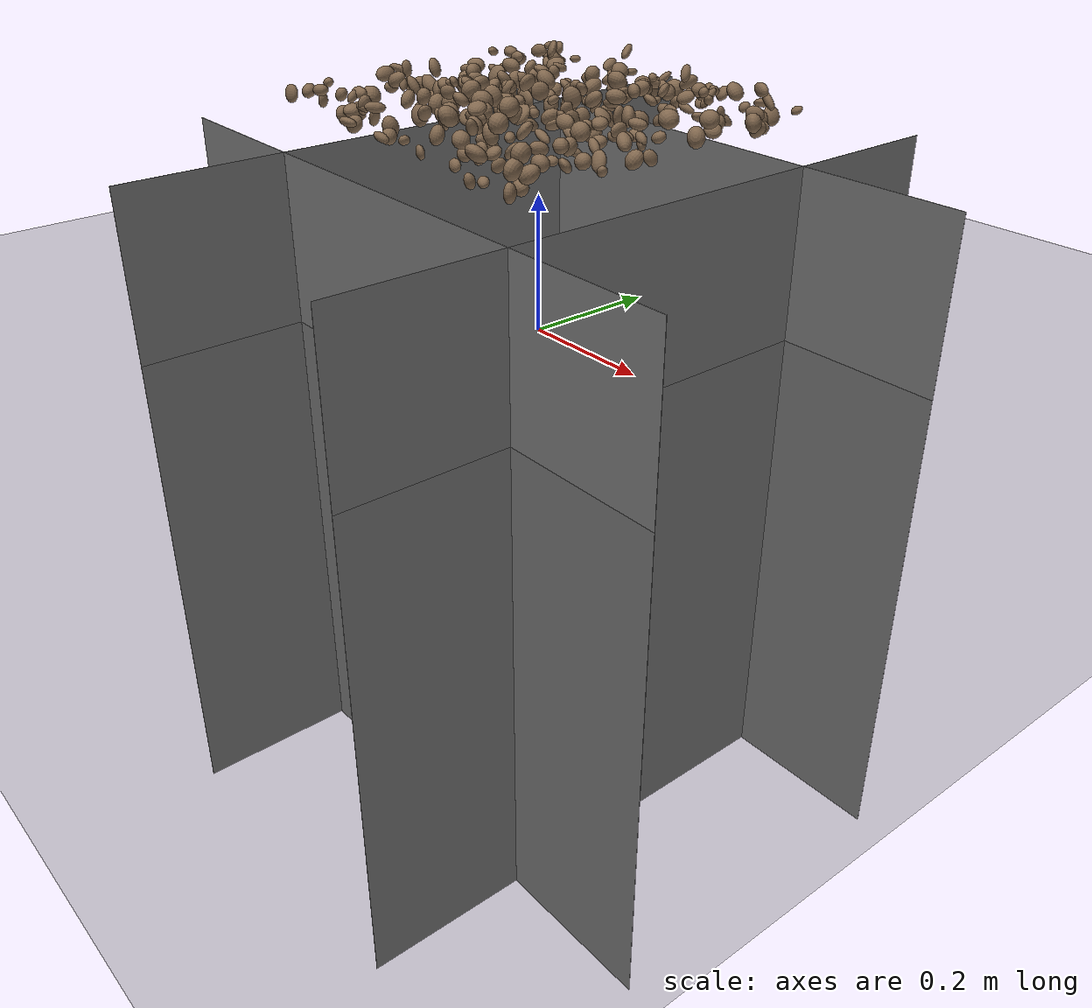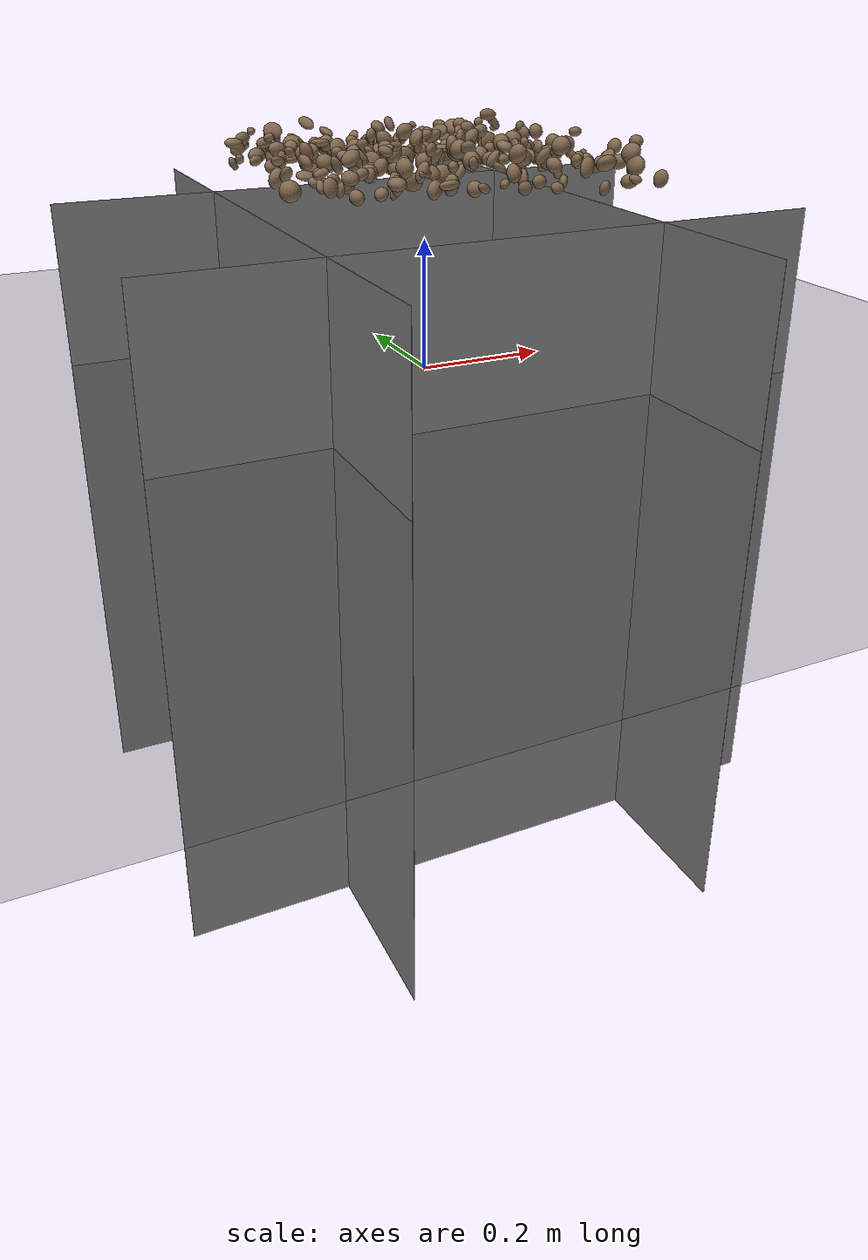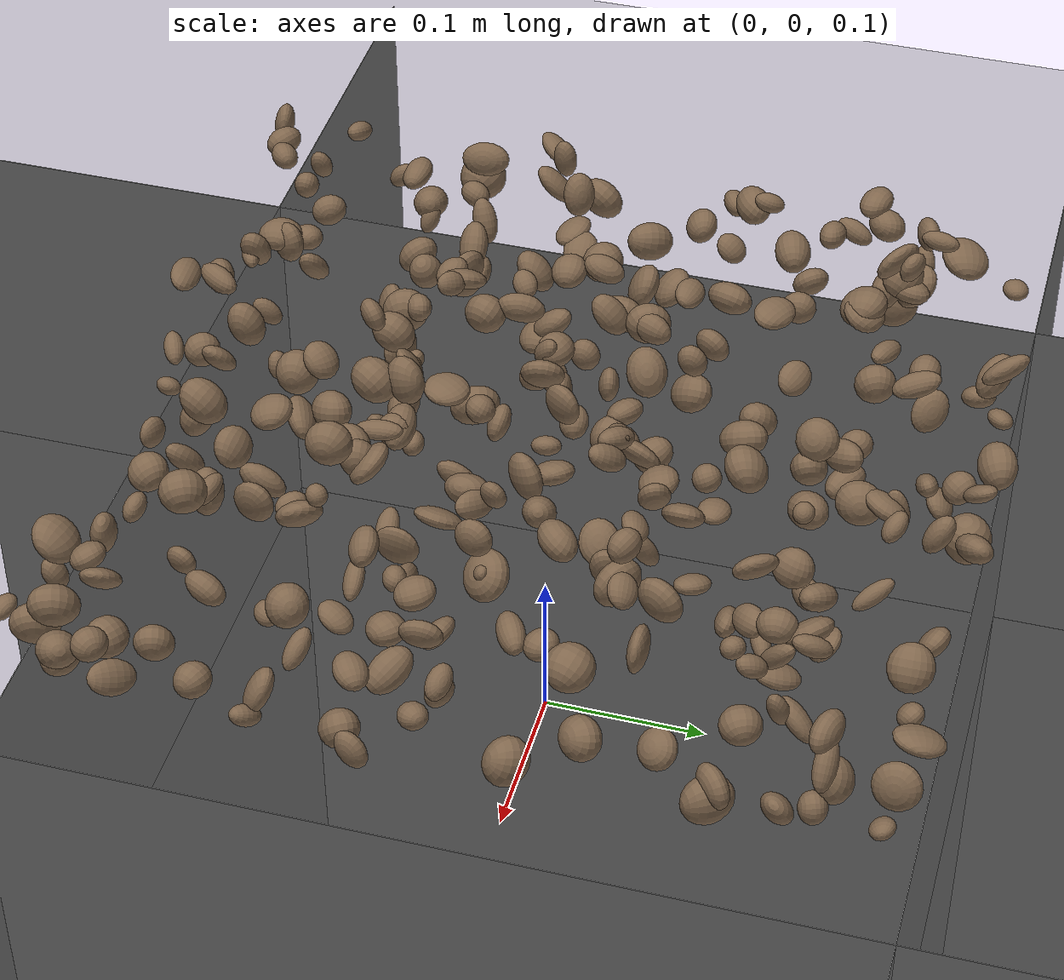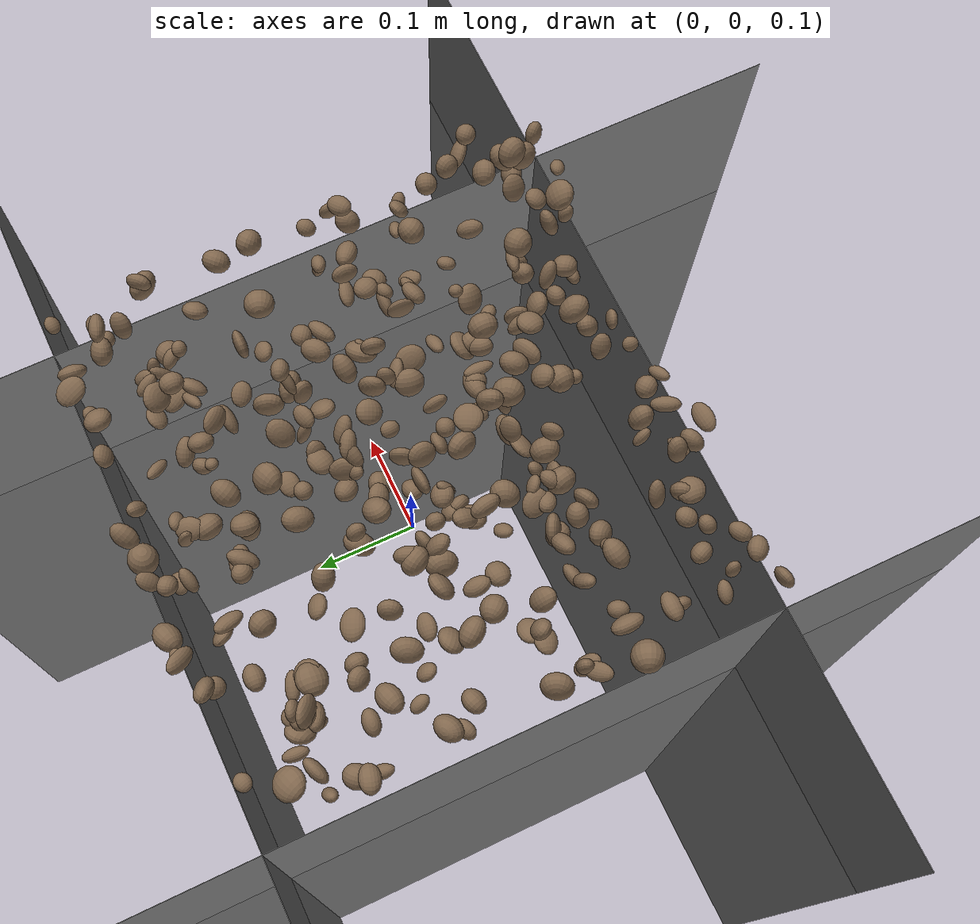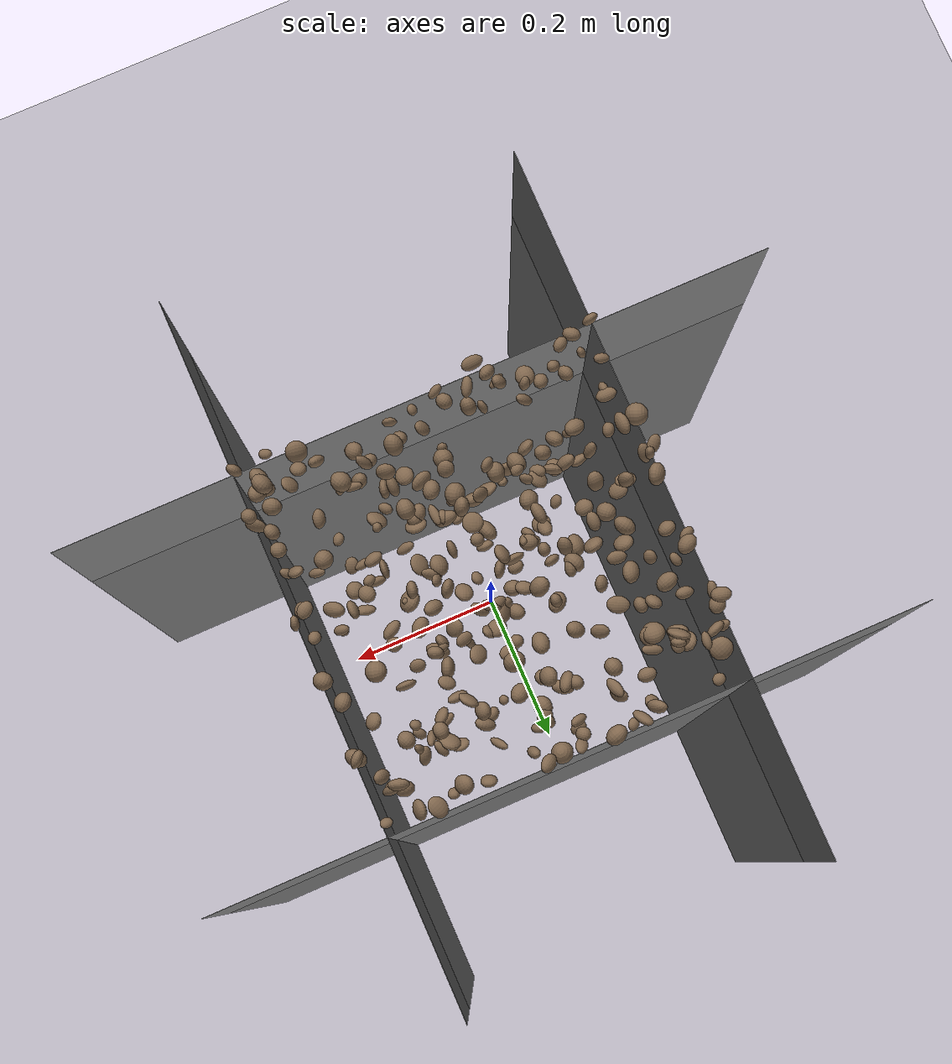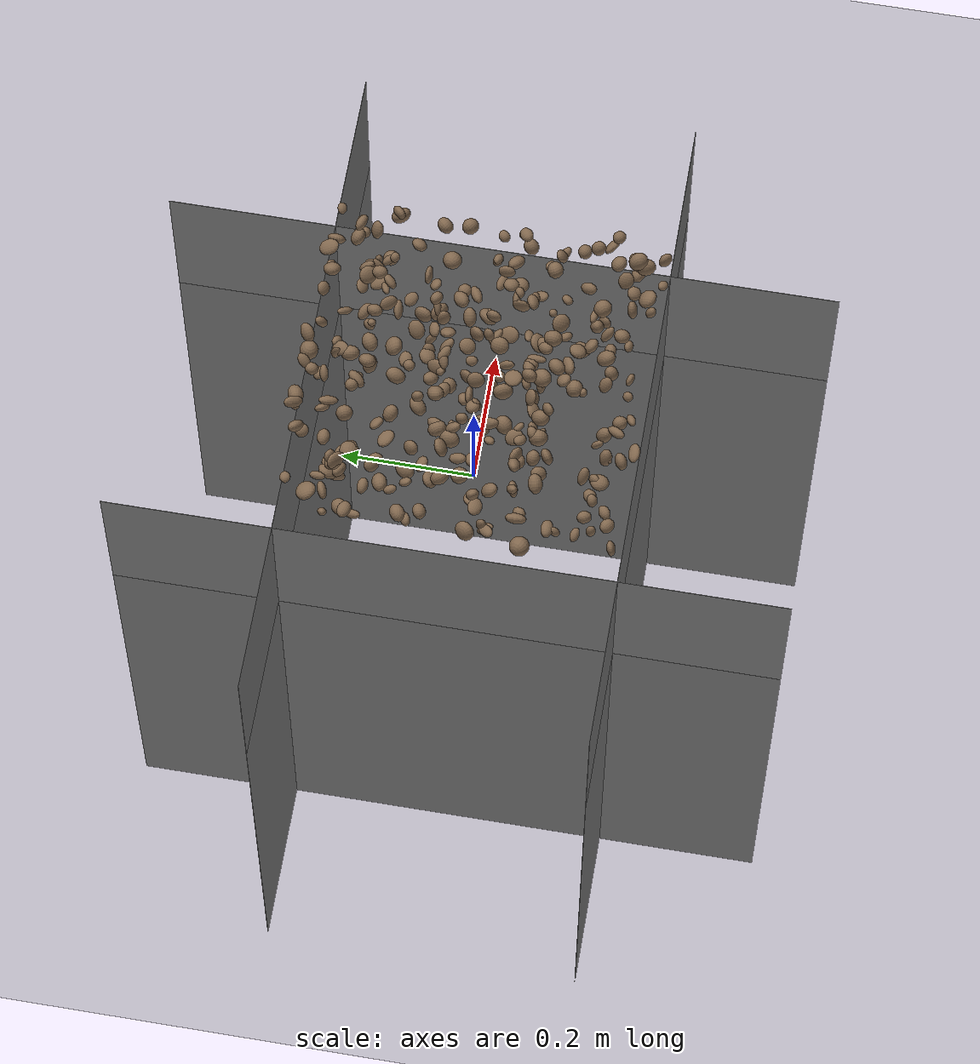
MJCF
<mujoco model="rocky_terrain_scene">

  <default>
    <default class="wall">
      <geom type="plane" size=".5 .5 .05" />
    </default>
  </default>

    <compiler angle="radian" inertiafromgeom="true" />
    <option timestep="0.002" gravity="0 0 -9.81" />

    <worldbody>

        <geom name="+x" class="wall" zaxis="1 0 0" pos="-.25 0 -.25" />
        <geom name="-x" class="wall" zaxis="-1 0 0" pos=".25 0 -.25" />
        <geom name="+y" class="wall" zaxis="0 1 0" pos="0 -.25 -.25" />
        <geom name="-y" class="wall" zaxis="0 -1 0" pos="0 .25 -.25" />

        <light name="sunlight" pos="5 5 5" dir="-1 -1 -1" diffuse="1 1 1" specular="0.5 0.5 0.5" ambient="0.5 0.5 0.5" />

        <geom name="ground_plane" type="plane" size="50 50 0.1" rgba="0.3 0.3 0.3 1" />

        <body name="rocky_terrain_body">

        </body>
    <body name="rock1" pos="0.19885721035740173 -0.002353968716752697 0.31870427519916933"><joint type="free" /><geom type="ellipsoid" size="0.010533199077717157 0.006737862992738098 0.00631333475504077" quat="0.004868014991842969 0.17773194804753886 0.21449477435578934 0.6029052626048289" rgba="0.5 0.4 0.3 1" /><inertial pos="0.19885721035740173 -0.002353968716752697 0.31870427519916933" quat="0.004868014991842969 0.17773194804753886 0.21449477435578934 0.6029052626048289" mass="7.405304663777684e-05" /></body><body name="rock2" pos="0.06041816094157676 0.07283723806865694 0.303896656949404"><joint type="free" /><geom type="ellipsoid" size="0.0053801803856945996 0.013338227454031099 0.0062474510997707735" quat="0.3325082138489068 0.5502749441139881 0.09076829778247898 0.026448544254626023" rgba="0.5 0.4 0.3 1" /><inertial pos="0.06041816094157676 0.07283723806865694 0.303896656949404" quat="0.3325082138489068 0.5502749441139881 0.09076829778247898 0.026448544254626023" mass="5.749188929571722e-05" /></body><body name="rock3" pos="-0.21855658921089605 -0.152539164046751 0.3164543384365317"><joint type="free" /><geom type="ellipsoid" size="0.006572346444566703 0.009942367876351223 0.005811593165738158" quat="0.3344074634426393 0.15183539817479422 0.3585116191651713 0.15524551921739518" rgba="0.5 0.4 0.3 1" /><inertial pos="-0.21855658921089605 -0.152539164046751 0.3164543384365317" quat="0.3344074634426393 0.15183539817479422 0.3585116191651713 0.15524551921739518" mass="4.410274069558521e-05" /></body><body name="rock4" pos="-0.20282648103857404 0.12458346861967656 0.33659876183766513"><joint type="free" /><geom type="ellipsoid" size="0.007761120310313378 0.011945204087987096 0.007929003597949348" quat="0.04754807859012079 0.4616329287057 0.42001151315867086 0.07080747954550828" rgba="0.5 0.4 0.3 1" /><inertial pos="-0.20282648103857404 0.12458346861967656 0.33659876183766513" quat="0.04754807859012079 0.4616329287057 0.42001151315867086 0.07080747954550828" mass="3.803749399163293e-05" /></body><body name="rock5" pos="-0.12290470488582883 0.1055343191872406 0.33441557603645433"><joint type="free" /><geom type="ellipsoid" size="0.014504680439422445 0.005879388739351867 0.010903532116276411" quat="0.09724829814256257 0.09640155710492417 0.45333012356974 0.3530200211827733" rgba="0.5 0.4 0.3 1" /><inertial pos="-0.12290470488582883 0.1055343191872406 0.33441557603645433" quat="0.09724829814256257 0.09640155710492417 0.45333012356974 0.3530200211827733" mass="8.819586361999056e-05" /></body><body name="rock6" pos="0.023545932225031763 0.07160555378442907 0.3213753372262984"><joint type="free" /><geom type="ellipsoid" size="0.012608158826840372 0.007439997892429669 0.011593025769274914" quat="0.3616057549307779 0.5024442365413176 0.0553300795797666 0.08061992894813787" rgba="0.5 0.4 0.3 1" /><inertial pos="0.023545932225031763 0.07160555378442907 0.3213753372262984" quat="0.3616057549307779 0.5024442365413176 0.0553300795797666 0.08061992894813787" mass="8.415947815627164e-05" /></body><body name="rock7" pos="-0.20022789172382144 0.23720363243916748 0.31996071938150755"><joint type="free" /><geom type="ellipsoid" size="0.007714013225497175 0.005462844179594916 0.008438194131886304" quat="0.2389063470398093 0.19492540789292356 0.2831013900729424 0.2830668549943247" rgba="0.5 0.4 0.3 1" /><inertial pos="-0.20022789172382144 0.23720363243916748 0.31996071938150755" quat="0.2389063470398093 0.19492540789292356 0.2831013900729424 0.2830668549943247" mass="9.482149606577855e-05" /></body><body name="rock8" pos="-0.05347476972039639 -0.00797660452415938 0.33781770407468886"><joint type="free" /><geom type="ellipsoid" size="0.01044719991491722 0.008401874058523506 0.01140105477649865" quat="0.33041489586217615 0.2649356381749095 0.2731643978538317 0.1314850681090826" rgba="0.5 0.4 0.3 1" /><inertial pos="-0.05347476972039639 -0.00797660452415938 0.33781770407468886" quat="0.33041489586217615 0.2649356381749095 0.2731643978538317 0.1314850681090826" mass="7.378041957568164e-05" /></body><body name="rock9" pos="-0.15739436002592155 -0.006652732900499281 0.3232351479069051"><joint type="free" /><geom type="ellipsoid" size="0.01191994781241763 0.011985221160701042 0.012623338011311956" quat="0.280874310522404 0.44129100488424144 0.13127525865020576 0.14655942594314883" rgba="0.5 0.4 0.3 1" /><inertial pos="-0.15739436002592155 -0.006652732900499281 0.3232351479069051" quat="0.280874310522404 0.44129100488424144 0.13127525865020576 0.14655942594314883" mass="6.172317223482526e-05" /></body><body name="rock10" pos="0.1801694023842561 0.06223965031488121 0.32831167682033824"><joint type="free" /><geom type="ellipsoid" size="0.013741324607750245 0.012424445408947583 0.013481165678860915" quat="0.23825510319282348 0.33968286925419905 0.25606094140245467 0.16600108615052284" rgba="0.5 0.4 0.3 1" /><inertial pos="0.1801694023842561 0.06223965031488121 0.32831167682033824" quat="0.23825510319282348 0.33968286925419905 0.25606094140245467 0.16600108615052284" mass="8.078100438738166e-05" /></body><body name="rock11" pos="0.021522532425880425 0.006645525989897205 0.33151083903635065"><joint type="free" /><geom type="ellipsoid" size="0.005583772064504088 0.008670686309916006 0.007527902233574475" quat="0.6278358434856912 0.014913086617003723 0.31515680040802485 0.04209426948928012" rgba="0.5 0.4 0.3 1" /><inertial pos="0.021522532425880425 0.006645525989897205 0.33151083903635065" quat="0.6278358434856912 0.014913086617003723 0.31515680040802485 0.04209426948928012" mass="1.8445973838332495e-05" /></body><body name="rock12" pos="0.21768298551717757 -0.17687735753311973 0.3235948924803359"><joint type="free" /><geom type="ellipsoid" size="0.011329791510323425 0.01003370657804869 0.012261738739452632" quat="0.404148524850821 0.228090371184493 0.2720913210376592 0.09566978292702681" rgba="0.5 0.4 0.3 1" /><inertial pos="0.21768298551717757 -0.17687735753311973 0.3235948924803359" quat="0.404148524850821 0.228090371184493 0.2720913210376592 0.09566978292702681" mass="4.623170637779394e-05" /></body><body name="rock13" pos="0.07976624472763233 0.158361164529972 0.3299444596948309"><joint type="free" /><geom type="ellipsoid" size="0.011616522596505818 0.008971991068485213 0.011252654947361617" quat="0.14511551732394587 0.43539225119371705 0.376896673576033 0.042595557906303996" rgba="0.5 0.4 0.3 1" /><inertial pos="0.07976624472763233 0.158361164529972 0.3299444596948309" quat="0.14511551732394587 0.43539225119371705 0.376896673576033 0.042595557906303996" mass="5.4293436723836304e-05" /></body><body name="rock14" pos="0.15153065947170186 0.23522626211103226 0.3116298947735203"><joint type="free" /><geom type="ellipsoid" size="0.008430397544418877 0.006316082032196848 0.007538689411664617" quat="0.22748530339742978 0.47963439659724694 0.04601624513070152 0.24686405487462174" rgba="0.5 0.4 0.3 1" /><inertial pos="0.15153065947170186 0.23522626211103226 0.3116298947735203" quat="0.22748530339742978 0.47963439659724694 0.04601624513070152 0.24686405487462174" mass="8.068229937700634e-05" /></body><body name="rock15" pos="-0.219069259221655 0.18008777499664308 0.33636770663671006"><joint type="free" /><geom type="ellipsoid" size="0.006397805663963697 0.013452239815673034 0.00930908848628145" quat="0.06360537163422834 0.36374038096181466 0.5293441734133343 0.04331007399062284" rgba="0.5 0.4 0.3 1" /><inertial pos="-0.219069259221655 0.18008777499664308 0.33636770663671006" quat="0.06360537163422834 0.36374038096181466 0.5293441734133343 0.04331007399062284" mass="4.168756596269916e-05" /></body><body name="rock16" pos="0.07920677290803335 -0.03886004559816325 0.31746476481289654"><joint type="free" /><geom type="ellipsoid" size="0.012550532833043351 0.013986461195447466 0.0053360138895286666" quat="0.07576458122159554 0.6467915513488273 0.07612288416177843 0.20132098326779876" rgba="0.5 0.4 0.3 1" /><inertial pos="0.07920677290803335 -0.03886004559816325 0.31746476481289654" quat="0.07576458122159554 0.6467915513488273 0.07612288416177843 0.20132098326779876" mass="5.865432668449661e-05" /></body><body name="rock17" pos="-0.09211529975184563 0.014368602709606382 0.3379993583130224"><joint type="free" /><geom type="ellipsoid" size="0.014108698907074849 0.0076308794395176524 0.009226673274580165" quat="0.3293775654240809 0.2458147704647772 0.4016024093521597 0.02320525475898216" rgba="0.5 0.4 0.3 1" /><inertial pos="-0.09211529975184563 0.014368602709606382 0.3379993583130224" quat="0.3293775654240809 0.2458147704647772 0.4016024093521597 0.02320525475898216" mass="3.7765857430783745e-05" /></body><body name="rock18" pos="-0.0574127641682165 0.07133781795959265 0.3193385618912774"><joint type="free" /><geom type="ellipsoid" size="0.014903635671573889 0.010098912493743385 0.011481996197686362" quat="0.0897419939911476 0.4914094756690027 0.19241885772114592 0.22642967261870373" rgba="0.5 0.4 0.3 1" /><inertial pos="-0.0574127641682165 0.07133781795959265 0.3193385618912774" quat="0.0897419939911476 0.4914094756690027 0.19241885772114592 0.22642967261870373" mass="3.7708381048472376e-05" /></body><body name="rock19" pos="0.22457643415457768 0.1811197634642786 0.304320606510919"><joint type="free" /><geom type="ellipsoid" size="0.009634516341565834 0.0069177457705775075 0.01367428357725231" quat="0.49132243309892365 0.09677834500351976 0.152802420684795 0.25909680121276163" rgba="0.5 0.4 0.3 1" /><inertial pos="0.22457643415457768 0.1811197634642786 0.304320606510919" quat="0.49132243309892365 0.09677834500351976 0.152802420684795 0.25909680121276163" mass="5.223498510071574e-05" /></body><body name="rock20" pos="0.010323117160493556 0.1817007311972933 0.32061029949110764"><joint type="free" /><geom type="ellipsoid" size="0.013755451075366004 0.012578803413939963 0.01079899727966947" quat="0.33351197733206994 0.13497449012573584 0.2509783617527403 0.2805351707894539" rgba="0.5 0.4 0.3 1" /><inertial pos="0.010323117160493556 0.1817007311972933 0.32061029949110764" quat="0.33351197733206994 0.13497449012573584 0.2509783617527403 0.2805351707894539" mass="2.7509931515030358e-05" /></body><body name="rock21" pos="-0.005149688379464723 0.15013234757138444 0.32560245433830026"><joint type="free" /><geom type="ellipsoid" size="0.0103016688225139 0.014206612343644846 0.009563432184244061" quat="0.10111771475538309 0.3282575944346577 0.33721993576943415 0.233404755040525" rgba="0.5 0.4 0.3 1" /><inertial pos="-0.005149688379464723 0.15013234757138444 0.32560245433830026" quat="0.10111771475538309 0.3282575944346577 0.33721993576943415 0.233404755040525" mass="1.3231239089580949e-05" /></body><body name="rock22" pos="0.053645969135724614 -0.14211451700662242 0.34927066097232906"><joint type="free" /><geom type="ellipsoid" size="0.012405960673224251 0.007411036128421452 0.011688108043232889" quat="0.15393604928003277 0.28701319715855583 0.25949079432991135 0.2995599592315001" rgba="0.5 0.4 0.3 1" /><inertial pos="0.053645969135724614 -0.14211451700662242 0.34927066097232906" quat="0.15393604928003277 0.28701319715855583 0.25949079432991135 0.2995599592315001" mass="3.7788957661691163e-05" /></body><body name="rock23" pos="-0.09483837913267706 -0.07447473666661181 0.34405216029966923"><joint type="free" /><geom type="ellipsoid" size="0.011298554037027697 0.013448544588975962 0.0059391353706682555" quat="0.0689463442296789 0.5408791551556267 0.21902560624314393 0.17114889437155054" rgba="0.5 0.4 0.3 1" /><inertial pos="-0.09483837913267706 -0.07447473666661181 0.34405216029966923" quat="0.0689463442296789 0.5408791551556267 0.21902560624314393 0.17114889437155054" mass="4.160741174439486e-05" /></body><body name="rock24" pos="0.24485881198881582 -0.1632655324590238 0.32430419492545476"><joint type="free" /><geom type="ellipsoid" size="0.0059642343431378815 0.009767517509952731 0.014320421025425495" quat="0.34537136178929734 0.30914183461180456 0.019759690237710906 0.32572711336118715" rgba="0.5 0.4 0.3 1" /><inertial pos="0.24485881198881582 -0.1632655324590238 0.32430419492545476" quat="0.34537136178929734 0.30914183461180456 0.019759690237710906 0.32572711336118715" mass="4.665070202538459e-05" /></body><body name="rock25" pos="-0.15154855445040916 -0.19323055261493838 0.30886908296483906"><joint type="free" /><geom type="ellipsoid" size="0.009097454614935614 0.008019357457886903 0.010367028785083514" quat="0.21106107406984023 0.08845924754216578 0.28777415457222516 0.4127055238157687" rgba="0.5 0.4 0.3 1" /><inertial pos="-0.15154855445040916 -0.19323055261493838 0.30886908296483906" quat="0.21106107406984023 0.08845924754216578 0.28777415457222516 0.4127055238157687" mass="7.647069275306454e-05" /></body><body name="rock26" pos="0.14248479345620096 0.020170779734020206 0.3053380108449193"><joint type="free" /><geom type="ellipsoid" size="0.008242303071512837 0.007533413144299329 0.014099314428239529" quat="0.01362897591040789 0.3727879000344822 0.22020377812224137 0.3933793459328686" rgba="0.5 0.4 0.3 1" /><inertial pos="0.14248479345620096 0.020170779734020206 0.3053380108449193" quat="0.01362897591040789 0.3727879000344822 0.22020377812224137 0.3933793459328686" mass="8.261655615054494e-05" /></body><body name="rock27" pos="-0.11780670430948453 -0.0805622705679106 0.3316196359115807"><joint type="free" /><geom type="ellipsoid" size="0.013087123516316607 0.013873794786421867 0.006575649810204814" quat="0.01609029201555935 0.19443597575832294 0.4038295371389565 0.38564419508716113" rgba="0.5 0.4 0.3 1" /><inertial pos="-0.11780670430948453 -0.0805622705679106 0.3316196359115807" quat="0.01609029201555935 0.19443597575832294 0.4038295371389565 0.38564419508716113" mass="1.1833323208734345e-05" /></body><body name="rock28" pos="0.15273403850049716 -0.02916101608587468 0.3320036352290878"><joint type="free" /><geom type="ellipsoid" size="0.010520277949961111 0.00790287944173117 0.011413921807462871" quat="0.36635014617978134 0.4411344320925567 0.12796815717606766 0.06454726455159432" rgba="0.5 0.4 0.3 1" /><inertial pos="0.15273403850049716 -0.02916101608587468 0.3320036352290878" quat="0.36635014617978134 0.4411344320925567 0.12796815717606766 0.06454726455159432" mass="4.1252480160460414e-05" /></body><body name="rock29" pos="0.20009025853290124 -0.24446307322101596 0.31084108985461123"><joint type="free" /><geom type="ellipsoid" size="0.008906974323989998 0.005626724696532522 0.00677892289891081" quat="0.06071912394330266 0.16078240445178307 0.31533475872020184 0.4631637128847125" rgba="0.5 0.4 0.3 1" /><inertial pos="0.20009025853290124 -0.24446307322101596 0.31084108985461123" quat="0.06071912394330266 0.16078240445178307 0.31533475872020184 0.4631637128847125" mass="7.884780275614236e-05" /></body><body name="rock30" pos="-0.07139598127984165 -0.19098169334911952 0.3130091552918758"><joint type="free" /><geom type="ellipsoid" size="0.01056891451255529 0.006587409926250878 0.005023507917677034" quat="0.36046646479686917 0.06710435773371376 0.35498833149036363 0.21744084597905344" rgba="0.5 0.4 0.3 1" /><inertial pos="-0.07139598127984165 -0.19098169334911952 0.3130091552918758" quat="0.36046646479686917 0.06710435773371376 0.35498833149036363 0.21744084597905344" mass="2.2458551612804757e-05" /></body><body name="rock31" pos="0.08139539307508292 -0.14587408362039656 0.30535735908416317"><joint type="free" /><geom type="ellipsoid" size="0.014346462862343524 0.012492640444215159 0.006410242737793829" quat="0.11738913206504106 0.4490938237103544 0.022455567480778472 0.4110614767438262" rgba="0.5 0.4 0.3 1" /><inertial pos="0.08139539307508292 -0.14587408362039656 0.30535735908416317" quat="0.11738913206504106 0.4490938237103544 0.022455567480778472 0.4110614767438262" mass="7.433866522456062e-05" /></body><body name="rock32" pos="0.0705999159945307 0.04990076766546392 0.3132585660001205"><joint type="free" /><geom type="ellipsoid" size="0.011398852013144948 0.013265741639203944 0.006751236335315" quat="0.301520185703467 0.13607464258393806 0.1516924589249212 0.4107127127876737" rgba="0.5 0.4 0.3 1" /><inertial pos="0.0705999159945307 0.04990076766546392 0.3132585660001205" quat="0.301520185703467 0.13607464258393806 0.1516924589249212 0.4107127127876737" mass="9.525589379968082e-05" /></body><body name="rock33" pos="0.2436906919638419 -0.24151938868892842 0.3079056968270949"><joint type="free" /><geom type="ellipsoid" size="0.010081885355444799 0.012561488233053567 0.007150681236498365" quat="0.10953699299891516 0.2125525538324681 0.32251769461147933 0.3553927585571374" rgba="0.5 0.4 0.3 1" /><inertial pos="0.2436906919638419 -0.24151938868892842 0.3079056968270949" quat="0.10953699299891516 0.2125525538324681 0.32251769461147933 0.3553927585571374" mass="1.594551519289921e-05" /></body><body name="rock34" pos="0.16849675277628495 0.16956179102454833 0.31505753534914827"><joint type="free" /><geom type="ellipsoid" size="0.005836542599050697 0.012360795411847803 0.0052577465750347175" quat="0.2175010178064549 0.33276640994452183 0.22813788527001336 0.22159468697900994" rgba="0.5 0.4 0.3 1" /><inertial pos="0.16849675277628495 0.16956179102454833 0.31505753534914827" quat="0.2175010178064549 0.33276640994452183 0.22813788527001336 0.22159468697900994" mass="2.7120943082035972e-05" /></body><body name="rock35" pos="0.16255329697503668 -0.013920187582997401 0.316034990665133"><joint type="free" /><geom type="ellipsoid" size="0.007523297394106966 0.0057403896749470915 0.013072089879806462" quat="0.20953880124554342 0.3530857969649496 0.10843654550350977 0.32893885628599717" rgba="0.5 0.4 0.3 1" /><inertial pos="0.16255329697503668 -0.013920187582997401 0.316034990665133" quat="0.20953880124554342 0.3530857969649496 0.10843654550350977 0.32893885628599717" mass="7.196566132365374e-05" /></body><body name="rock36" pos="0.03027181464657419 -0.07868372786193767 0.33103065746969423"><joint type="free" /><geom type="ellipsoid" size="0.010386528054518934 0.010131776164384243 0.009278354543556848" quat="0.1896509908369071 0.29572900541450653 0.23093791622464918 0.28368208752393714" rgba="0.5 0.4 0.3 1" /><inertial pos="0.03027181464657419 -0.07868372786193767 0.33103065746969423" quat="0.1896509908369071 0.29572900541450653 0.23093791622464918 0.28368208752393714" mass="8.248842365215016e-05" /></body><body name="rock37" pos="-0.04334236834551547 0.0479293956542764 0.3413506670612145"><joint type="free" /><geom type="ellipsoid" size="0.011672891618048162 0.014641279741494637 0.010601857428100367" quat="0.28295839709800313 0.13969776762045857 0.1609825479647347 0.4163612873168037" rgba="0.5 0.4 0.3 1" /><inertial pos="-0.04334236834551547 0.0479293956542764 0.3413506670612145" quat="0.28295839709800313 0.13969776762045857 0.1609825479647347 0.4163612873168037" mass="3.7674909533544446e-05" /></body><body name="rock38" pos="-0.006760400137061695 0.061403536449154195 0.313108058703851"><joint type="free" /><geom type="ellipsoid" size="0.00975487357120035 0.009579699227154025 0.011822869113097951" quat="0.2950848090460089 0.4165472250184045 0.25609956137024587 0.032268404565340664" rgba="0.5 0.4 0.3 1" /><inertial pos="-0.006760400137061695 0.061403536449154195 0.313108058703851" quat="0.2950848090460089 0.4165472250184045 0.25609956137024587 0.032268404565340664" mass="2.7623887179361262e-05" /></body><body name="rock39" pos="-0.16957711819285098 0.17790735884831987 0.347912193321771"><joint type="free" /><geom type="ellipsoid" size="0.009483822563370208 0.005818482000803909 0.009503200519024584" quat="0.16826166645477025 0.14851710403883253 0.037144914114748566 0.6460763153916486" rgba="0.5 0.4 0.3 1" /><inertial pos="-0.16957711819285098 0.17790735884831987 0.347912193321771" quat="0.16826166645477025 0.14851710403883253 0.037144914114748566 0.6460763153916486" mass="7.389937495180163e-05" /></body><body name="rock40" pos="0.16560373231802972 0.17905788363607822 0.3071956134537791"><joint type="free" /><geom type="ellipsoid" size="0.014481448550926014 0.006029455895661052 0.0077089038307085285" quat="0.4393654486609003 0.12515275288412647 0.2720483309393701 0.16343346751560317" rgba="0.5 0.4 0.3 1" /><inertial pos="0.16560373231802972 0.17905788363607822 0.3071956134537791" quat="0.4393654486609003 0.12515275288412647 0.2720483309393701 0.16343346751560317" mass="7.111031184844673e-05" /></body><body name="rock41" pos="0.09803483619616432 -0.1997161383919957 0.3296839578362232"><joint type="free" /><geom type="ellipsoid" size="0.011731793615095762 0.010065515178693012 0.011186067639765054" quat="0.01948177128676623 0.2994289729543927 0.35057231713708686 0.3305169386217543" rgba="0.5 0.4 0.3 1" /><inertial pos="0.09803483619616432 -0.1997161383919957 0.3296839578362232" quat="0.01948177128676623 0.2994289729543927 0.35057231713708686 0.3305169386217543" mass="7.805253756342969e-05" /></body><body name="rock42" pos="-0.014681536820582375 -0.08823292092571133 0.310052391372665"><joint type="free" /><geom type="ellipsoid" size="0.008643466009173869 0.012863187388881633 0.014566183259691223" quat="0.27877454567315724 0.23479500156438532 0.27099952711369363 0.2154309256487638" rgba="0.5 0.4 0.3 1" /><inertial pos="-0.014681536820582375 -0.08823292092571133 0.310052391372665" quat="0.27877454567315724 0.23479500156438532 0.27099952711369363 0.2154309256487638" mass="7.419872748608915e-05" /></body><body name="rock43" pos="0.06790563204782069 -0.010674229404182556 0.3311755764199172"><joint type="free" /><geom type="ellipsoid" size="0.0055265586251701795 0.010346697746107313 0.00808875805625774" quat="0.005208437418736569 0.15696630237236495 0.458951361326596 0.3788738988823025" rgba="0.5 0.4 0.3 1" /><inertial pos="0.06790563204782069 -0.010674229404182556 0.3311755764199172" quat="0.005208437418736569 0.15696630237236495 0.458951361326596 0.3788738988823025" mass="5.0043668818123275e-05" /></body><body name="rock44" pos="-0.02833662150765126 0.16548024028701408 0.3184577749040462"><joint type="free" /><geom type="ellipsoid" size="0.008248844976750942 0.0147570781376344 0.009449243160511048" quat="0.129130551449301 0.21322871657950127 0.5700567286591924 0.08758400331200543" rgba="0.5 0.4 0.3 1" /><inertial pos="-0.02833662150765126 0.16548024028701408 0.3184577749040462" quat="0.129130551449301 0.21322871657950127 0.5700567286591924 0.08758400331200543" mass="9.200321564973665e-05" /></body><body name="rock45" pos="-0.051913264257911707 -0.10539364120480932 0.33097999537823286"><joint type="free" /><geom type="ellipsoid" size="0.012320072235162384 0.013343949345937342 0.010802995569091735" quat="0.15677119500032322 0.4547163480002388 0.07312888002179865 0.3153835769776393" rgba="0.5 0.4 0.3 1" /><inertial pos="-0.051913264257911707 -0.10539364120480932 0.33097999537823286" quat="0.15677119500032322 0.4547163480002388 0.07312888002179865 0.3153835769776393" mass="7.360217367508801e-05" /></body><body name="rock46" pos="-0.009071128051469868 0.15284803087059123 0.34380463397314787"><joint type="free" /><geom type="ellipsoid" size="0.012278960100919018 0.01226986531020069 0.009595726099223927" quat="0.4005336199786632 0.16317306425871989 0.16251081811699816 0.2737824976456188" rgba="0.5 0.4 0.3 1" /><inertial pos="-0.009071128051469868 0.15284803087059123 0.34380463397314787" quat="0.4005336199786632 0.16317306425871989 0.16251081811699816 0.2737824976456188" mass="1.2125777832807217e-05" /></body><body name="rock47" pos="-0.2318704297568226 -0.05630616506593328 0.3188930455319351"><joint type="free" /><geom type="ellipsoid" size="0.006100808036774573 0.014601820029740878 0.008341722464534355" quat="0.1438808761503666 0.3498822652532735 0.14932941131109284 0.3569074472852671" rgba="0.5 0.4 0.3 1" /><inertial pos="-0.2318704297568226 -0.05630616506593328 0.3188930455319351" quat="0.1438808761503666 0.3498822652532735 0.14932941131109284 0.3569074472852671" mass="8.972374833051368e-05" /></body><body name="rock48" pos="0.0214116243774366 0.11964771275612679 0.3408004956991634"><joint type="free" /><geom type="ellipsoid" size="0.011013510519124838 0.014098109608913615 0.013752798813651646" quat="0.08622332847746549 0.3354558557929911 0.2428957779077107 0.3354250378218328" rgba="0.5 0.4 0.3 1" /><inertial pos="0.0214116243774366 0.11964771275612679 0.3408004956991634" quat="0.08622332847746549 0.3354558557929911 0.2428957779077107 0.3354250378218328" mass="9.232577135191795e-05" /></body><body name="rock49" pos="0.08539906901148203 0.020168006973225294 0.34178304888363825"><joint type="free" /><geom type="ellipsoid" size="0.009392938643201175 0.008862360389806694 0.014246255067046215" quat="0.3701356728343098 0.11069888373845772 0.1937124261805297 0.32545301724670267" rgba="0.5 0.4 0.3 1" /><inertial pos="0.08539906901148203 0.020168006973225294 0.34178304888363825" quat="0.3701356728343098 0.11069888373845772 0.1937124261805297 0.32545301724670267" mass="5.1499122829755864e-05" /></body><body name="rock50" pos="0.10651178110136028 -0.1619514958339941 0.33175005396649215"><joint type="free" /><geom type="ellipsoid" size="0.009448063366199373 0.009702747502042022 0.013958341337419865" quat="0.08728474227036921 0.27858332166715044 0.5800184073507964 0.0541135287116839" rgba="0.5 0.4 0.3 1" /><inertial pos="0.10651178110136028 -0.1619514958339941 0.33175005396649215" quat="0.08728474227036921 0.27858332166715044 0.5800184073507964 0.0541135287116839" mass="5.9039985812866175e-05" /></body><body name="rock51" pos="0.0913036053984998 0.05980463931558033 0.3160563164097552"><joint type="free" /><geom type="ellipsoid" size="0.009746294044282088 0.013999254867508665 0.006424108953450832" quat="0.1815523097808106 0.2620456430195816 0.28432802648097827 0.2720740207186295" rgba="0.5 0.4 0.3 1" /><inertial pos="0.0913036053984998 0.05980463931558033 0.3160563164097552" quat="0.1815523097808106 0.2620456430195816 0.28432802648097827 0.2720740207186295" mass="2.4335086313828592e-05" /></body><body name="rock52" pos="-0.148755637903924 0.15386429659550843 0.3295166571187965"><joint type="free" /><geom type="ellipsoid" size="0.014293194601088393 0.010770711996366897 0.014686440405691038" quat="0.21387906540887155 0.3007723728700115 0.18188766997532277 0.30346089174579416" rgba="0.5 0.4 0.3 1" /><inertial pos="-0.148755637903924 0.15386429659550843 0.3295166571187965" quat="0.21387906540887155 0.3007723728700115 0.18188766997532277 0.30346089174579416" mass="6.31427414641969e-05" /></body><body name="rock53" pos="0.19799331923482139 0.23670082542418253 0.30826920352913717"><joint type="free" /><geom type="ellipsoid" size="0.013386390021646984 0.013372311879174835 0.007180552436248107" quat="0.2543704587579513 0.24769688486834282 0.14286050399405872 0.3550721523796473" rgba="0.5 0.4 0.3 1" /><inertial pos="0.19799331923482139 0.23670082542418253 0.30826920352913717" quat="0.2543704587579513 0.24769688486834282 0.14286050399405872 0.3550721523796473" mass="2.566385137252199e-05" /></body><body name="rock54" pos="-0.020238799831151344 0.22253845666557914 0.3027721433922353"><joint type="free" /><geom type="ellipsoid" size="0.009619827875523106 0.0057195981092691365 0.010332105487513742" quat="0.3101199574218631 0.11859721732463291 0.40310101919113595 0.168181806062368" rgba="0.5 0.4 0.3 1" /><inertial pos="-0.020238799831151344 0.22253845666557914 0.3027721433922353" quat="0.3101199574218631 0.11859721732463291 0.40310101919113595 0.168181806062368" mass="2.1634467794149527e-05" /></body><body name="rock55" pos="-0.05939097336358895 0.24913471102934498 0.3034276476404502"><joint type="free" /><geom type="ellipsoid" size="0.011079720069455306 0.012050416770690096 0.014657296299635206" quat="0.24744827704012667 0.14865498959540255 0.4016593290317071 0.20223740433276366" rgba="0.5 0.4 0.3 1" /><inertial pos="-0.05939097336358895 0.24913471102934498 0.3034276476404502" quat="0.24744827704012667 0.14865498959540255 0.4016593290317071 0.20223740433276366" mass="3.747548469933339e-05" /></body><body name="rock56" pos="-0.12290112593207447 -0.17930193801456912 0.31055881110728845"><joint type="free" /><geom type="ellipsoid" size="0.007717381650143903 0.014978991603090894 0.006307972087856748" quat="0.1345043956913827 0.3381884046343607 0.3077137045020996 0.219593495172157" rgba="0.5 0.4 0.3 1" /><inertial pos="-0.12290112593207447 -0.17930193801456912 0.31055881110728845" quat="0.1345043956913827 0.3381884046343607 0.3077137045020996 0.219593495172157" mass="5.7266195489991095e-05" /></body><body name="rock57" pos="0.013484921768618596 0.19598924785404453 0.32462939999290097"><joint type="free" /><geom type="ellipsoid" size="0.01347390832487362 0.010540795119208721 0.006061133177642628" quat="0.1566971571690004 0.4944976285807326 0.3429274942330508 0.005877720017216188" rgba="0.5 0.4 0.3 1" /><inertial pos="0.013484921768618596 0.19598924785404453 0.32462939999290097" quat="0.1566971571690004 0.4944976285807326 0.3429274942330508 0.005877720017216188" mass="1.296007431142736e-05" /></body><body name="rock58" pos="0.24716250049856098 -0.17191948011359276 0.3485684777266433"><joint type="free" /><geom type="ellipsoid" size="0.009843259551706923 0.009179742739132819 0.009098930765060378" quat="0.12995049902417014 0.1538712058088604 0.33276919377371783 0.3834091013932516" rgba="0.5 0.4 0.3 1" /><inertial pos="0.24716250049856098 -0.17191948011359276 0.3485684777266433" quat="0.12995049902417014 0.1538712058088604 0.33276919377371783 0.3834091013932516" mass="4.744066814450044e-05" /></body><body name="rock59" pos="-0.09329613606754461 0.2443542588474747 0.34588726126292585"><joint type="free" /><geom type="ellipsoid" size="0.014956927906864339 0.0060221707515082665 0.008695285429313348" quat="0.23469956747758766 0.190833018375004 0.09531163781536806 0.47915577633204026" rgba="0.5 0.4 0.3 1" /><inertial pos="-0.09329613606754461 0.2443542588474747 0.34588726126292585" quat="0.23469956747758766 0.190833018375004 0.09531163781536806 0.47915577633204026" mass="4.127848960341447e-05" /></body><body name="rock60" pos="0.0008402267114395179 -0.14607851581231546 0.3342808511192733"><joint type="free" /><geom type="ellipsoid" size="0.012419049236038794 0.013281322132299819 0.012280501536186449" quat="0.23531242827758672 0.24648457565464005 0.24215471286353424 0.276048283204239" rgba="0.5 0.4 0.3 1" /><inertial pos="0.0008402267114395179 -0.14607851581231546 0.3342808511192733" quat="0.23531242827758672 0.24648457565464005 0.24215471286353424 0.276048283204239" mass="6.954359071220178e-05" /></body><body name="rock61" pos="-0.19695140899215235 -0.0355711517803915 0.31185285671517676"><joint type="free" /><geom type="ellipsoid" size="0.005864570543378569 0.010724205082711213 0.013440502888466519" quat="0.409974055226772 0.12776702184014782 0.4318199501724305 0.03043897276064968" rgba="0.5 0.4 0.3 1" /><inertial pos="-0.19695140899215235 -0.0355711517803915 0.31185285671517676" quat="0.409974055226772 0.12776702184014782 0.4318199501724305 0.03043897276064968" mass="4.9134803350531227e-05" /></body><body name="rock62" pos="0.1068743466301989 0.23874215068866628 0.3215083771056536"><joint type="free" /><geom type="ellipsoid" size="0.006498866414457112 0.010758294927646073 0.01031384276858071" quat="0.3294793232587383 0.2722213197960832 0.31283964137382203 0.08545971557135648" rgba="0.5 0.4 0.3 1" /><inertial pos="0.1068743466301989 0.23874215068866628 0.3215083771056536" quat="0.3294793232587383 0.2722213197960832 0.31283964137382203 0.08545971557135648" mass="4.177481785173422e-05" /></body><body name="rock63" pos="0.05180975732426718 0.15742127190535704 0.3446135503841346"><joint type="free" /><geom type="ellipsoid" size="0.0059408873384391245 0.006189588508836313 0.005135371539908765" quat="0.43066343235388005 0.10694718363146492 0.16099766062058568 0.30139172339406944" rgba="0.5 0.4 0.3 1" /><inertial pos="0.05180975732426718 0.15742127190535704 0.3446135503841346" quat="0.43066343235388005 0.10694718363146492 0.16099766062058568 0.30139172339406944" mass="7.44944385458996e-05" /></body><body name="rock64" pos="0.10502249894006671 0.07200996715804381 0.34802232601365296"><joint type="free" /><geom type="ellipsoid" size="0.008075729922757137 0.009284582605775322 0.01037331695411869" quat="0.267420246744001 0.3589201626968862 0.19720848980462333 0.17645110075448947" rgba="0.5 0.4 0.3 1" /><inertial pos="0.10502249894006671 0.07200996715804381 0.34802232601365296" quat="0.267420246744001 0.3589201626968862 0.19720848980462333 0.17645110075448947" mass="7.297185990156626e-05" /></body><body name="rock65" pos="-0.0804740268397171 -0.10711246094519439 0.3245098140584289"><joint type="free" /><geom type="ellipsoid" size="0.01365129451402326 0.014037247970035797 0.01125045146553395" quat="0.2953665837104719 0.14493321952007895 0.3438018168163752 0.2158983799530738" rgba="0.5 0.4 0.3 1" /><inertial pos="-0.0804740268397171 -0.10711246094519439 0.3245098140584289" quat="0.2953665837104719 0.14493321952007895 0.3438018168163752 0.2158983799530738" mass="7.847090709168413e-05" /></body><body name="rock66" pos="-0.07813487223209253 -0.024876304380598402 0.32440625782799304"><joint type="free" /><geom type="ellipsoid" size="0.012211826576287228 0.007828155028107232 0.012062801379690858" quat="0.19937913847874716 0.3478074134168253 0.21476079239388013 0.23805265571054737" rgba="0.5 0.4 0.3 1" /><inertial pos="-0.07813487223209253 -0.024876304380598402 0.32440625782799304" quat="0.19937913847874716 0.3478074134168253 0.21476079239388013 0.23805265571054737" mass="5.873460545096562e-05" /></body><body name="rock67" pos="-0.20203565496766235 0.18935412887135977 0.3452483571128947"><joint type="free" /><geom type="ellipsoid" size="0.011473068900300525 0.005801782151075228 0.005947112357120126" quat="0.3901099452780674 0.12587620658323542 0.14257716167776638 0.34143668646093067" rgba="0.5 0.4 0.3 1" /><inertial pos="-0.20203565496766235 0.18935412887135977 0.3452483571128947" quat="0.3901099452780674 0.12587620658323542 0.14257716167776638 0.34143668646093067" mass="9.605102629049541e-05" /></body><body name="rock68" pos="-0.14996680241280574 0.11528790972755432 0.31954824075963995"><joint type="free" /><geom type="ellipsoid" size="0.010424444950699632 0.010099476337307896 0.00845556918688587" quat="0.24604572758263682 0.23070781147211508 0.2714410193227751 0.251805441622473" rgba="0.5 0.4 0.3 1" /><inertial pos="-0.14996680241280574 0.11528790972755432 0.31954824075963995" quat="0.24604572758263682 0.23070781147211508 0.2714410193227751 0.251805441622473" mass="1.3840254401273735e-05" /></body><body name="rock69" pos="0.13618987900809615 0.23118066114293362 0.33021274239405846"><joint type="free" /><geom type="ellipsoid" size="0.012641676062769018 0.00948236669798977 0.013360482221689136" quat="0.15274055291180236 0.33173748156425364 0.3850637261262875 0.1304582393976565" rgba="0.5 0.4 0.3 1" /><inertial pos="0.13618987900809615 0.23118066114293362 0.33021274239405846" quat="0.15274055291180236 0.33173748156425364 0.3850637261262875 0.1304582393976565" mass="8.536010526030909e-05" /></body><body name="rock70" pos="0.2226049460665248 -0.09258134482076197 0.31166927109688697"><joint type="free" /><geom type="ellipsoid" size="0.006320800424751003 0.014048173124056245 0.009661238980999923" quat="0.30721426297207505 0.0997637558578031 0.3091263349165412 0.28389564625358066" rgba="0.5 0.4 0.3 1" /><inertial pos="0.2226049460665248 -0.09258134482076197 0.31166927109688697" quat="0.30721426297207505 0.0997637558578031 0.3091263349165412 0.28389564625358066" mass="2.4521994564948387e-05" /></body><body name="rock71" pos="-0.030431666050851236 -0.21736504693460973 0.3103714789787039"><joint type="free" /><geom type="ellipsoid" size="0.010779903946606665 0.01061531680792651 0.009809302773997487" quat="0.13319913919884474 0.21947267193467576 0.3231354862665513 0.32419270259992816" rgba="0.5 0.4 0.3 1" /><inertial pos="-0.030431666050851236 -0.21736504693460973 0.3103714789787039" quat="0.13319913919884474 0.21947267193467576 0.3231354862665513 0.32419270259992816" mass="9.627256440352106e-05" /></body><body name="rock72" pos="-0.24352645985667926 -0.058964496263703425 0.33769705650053616"><joint type="free" /><geom type="ellipsoid" size="0.00828706415184398 0.005486624792723346 0.012832659862548824" quat="0.1766820034626204 0.08094589185619448 0.4603608130878571 0.282011291593328" rgba="0.5 0.4 0.3 1" /><inertial pos="-0.24352645985667926 -0.058964496263703425 0.33769705650053616" quat="0.1766820034626204 0.08094589185619448 0.4603608130878571 0.282011291593328" mass="9.977213119333448e-05" /></body><body name="rock73" pos="0.23341123103057282 -0.09667141713253974 0.3028821494442152"><joint type="free" /><geom type="ellipsoid" size="0.006383673044255873 0.006063444113376934 0.010113392287570695" quat="0.3945046501786861 0.24393439650092433 0.06933268646965064 0.2922282668507389" rgba="0.5 0.4 0.3 1" /><inertial pos="0.23341123103057282 -0.09667141713253974 0.3028821494442152" quat="0.3945046501786861 0.24393439650092433 0.06933268646965064 0.2922282668507389" mass="9.930509936825805e-05" /></body><body name="rock74" pos="0.03449148380277278 -0.0419151549621421 0.3090134210911727"><joint type="free" /><geom type="ellipsoid" size="0.007953216028370857 0.012548869274004873 0.005562294090668123" quat="0.11325126089017963 0.4163642655587842 0.10830197975796568 0.3620824937930705" rgba="0.5 0.4 0.3 1" /><inertial pos="0.03449148380277278 -0.0419151549621421 0.3090134210911727" quat="0.11325126089017963 0.4163642655587842 0.10830197975796568 0.3620824937930705" mass="6.927725765771582e-05" /></body><body name="rock75" pos="-0.14216141513038622 0.17044889396959967 0.30367555685358466"><joint type="free" /><geom type="ellipsoid" size="0.013931885760998918 0.005774936503073397 0.00671914772791318" quat="0.12435025831622253 0.0486369063913515 0.48648063983833173 0.34053219545409424" rgba="0.5 0.4 0.3 1" /><inertial pos="-0.14216141513038622 0.17044889396959967 0.30367555685358466" quat="0.12435025831622253 0.0486369063913515 0.48648063983833173 0.34053219545409424" mass="3.2669292950054394e-05" /></body><body name="rock76" pos="0.05754630586589138 0.09312089783773803 0.3320773250167214"><joint type="free" /><geom type="ellipsoid" size="0.011763680670575434 0.01489605258752211 0.006491239936380009" quat="0.17952681332761233 0.290462181655973 0.41199601867604296 0.11801498634037175" rgba="0.5 0.4 0.3 1" /><inertial pos="0.05754630586589138 0.09312089783773803 0.3320773250167214" quat="0.17952681332761233 0.290462181655973 0.41199601867604296 0.11801498634037175" mass="5.068714278592383e-05" /></body><body name="rock77" pos="0.06021852026485458 0.0055329218607885755 0.3419311079513661"><joint type="free" /><geom type="ellipsoid" size="0.00733469229035612 0.011846790010284634 0.014425119127086671" quat="0.02356290546941586 0.21651250821927015 0.6427207363054739 0.11720385000583998" rgba="0.5 0.4 0.3 1" /><inertial pos="0.06021852026485458 0.0055329218607885755 0.3419311079513661" quat="0.02356290546941586 0.21651250821927015 0.6427207363054739 0.11720385000583998" mass="7.12042698283396e-05" /></body><body name="rock78" pos="-0.021541991232619184 0.2321250221112155 0.3158910338223596"><joint type="free" /><geom type="ellipsoid" size="0.009996074407968743 0.008748436515161596 0.009184952637271152" quat="0.0029675268915639727 0.2777778486212915 0.3546582458528625 0.364596378634282" rgba="0.5 0.4 0.3 1" /><inertial pos="-0.021541991232619184 0.2321250221112155 0.3158910338223596" quat="0.0029675268915639727 0.2777778486212915 0.3546582458528625 0.364596378634282" mass="7.37337005563684e-05" /></body><body name="rock79" pos="0.05066409654574866 -0.1835974058408218 0.34537055605125283"><joint type="free" /><geom type="ellipsoid" size="0.014968357482421896 0.011471593035016117 0.011657924251022836" quat="0.30179048517711415 0.26459429047696426 0.407081177666052 0.026534046679869604" rgba="0.5 0.4 0.3 1" /><inertial pos="0.05066409654574866 -0.1835974058408218 0.34537055605125283" quat="0.30179048517711415 0.26459429047696426 0.407081177666052 0.026534046679869604" mass="7.680198355385084e-05" /></body><body name="rock80" pos="0.1094277740345424 -0.0971723101665396 0.3469839479390157"><joint type="free" /><geom type="ellipsoid" size="0.006484546800897673 0.006168235928819285 0.005812589050987202" quat="0.46103893027864623 0.1754780722892102 0.30539974581648 0.0580832516156636" rgba="0.5 0.4 0.3 1" /><inertial pos="0.1094277740345424 -0.0971723101665396 0.3469839479390157" quat="0.46103893027864623 0.1754780722892102 0.30539974581648 0.0580832516156636" mass="3.056855676795772e-05" /></body><body name="rock81" pos="-0.18308439182513575 0.17900918767840424 0.3240492415904098"><joint type="free" /><geom type="ellipsoid" size="0.014968622544593878 0.008145083972221459 0.012659657585604429" quat="0.03830820927861796 0.34947211824757113 0.2671035668287276 0.34511610564508327" rgba="0.5 0.4 0.3 1" /><inertial pos="-0.18308439182513575 0.17900918767840424 0.3240492415904098" quat="0.03830820927861796 0.34947211824757113 0.2671035668287276 0.34511610564508327" mass="9.340483662022227e-05" /></body><body name="rock82" pos="-0.2069113111676006 -0.22606550135206221 0.3370228602425524"><joint type="free" /><geom type="ellipsoid" size="0.008527053631703977 0.009812539714075362 0.011341208404140034" quat="0.3742369712635449 0.2848043378710845 0.3060740202611496 0.034884670604221006" rgba="0.5 0.4 0.3 1" /><inertial pos="-0.2069113111676006 -0.22606550135206221 0.3370228602425524" quat="0.3742369712635449 0.2848043378710845 0.3060740202611496 0.034884670604221006" mass="5.451476312861095e-05" /></body><body name="rock83" pos="-0.13687242959857326 -0.0006834051771365535 0.33473735055299214"><joint type="free" /><geom type="ellipsoid" size="0.012700737492154042 0.008354570889151381 0.007448237068674939" quat="0.44606496863263867 0.00044825084856343336 0.1363221181845101 0.4171646623342878" rgba="0.5 0.4 0.3 1" /><inertial pos="-0.13687242959857326 -0.0006834051771365535 0.33473735055299214" quat="0.44606496863263867 0.00044825084856343336 0.1363221181845101 0.4171646623342878" mass="6.158754776445312e-05" /></body><body name="rock84" pos="0.10020595305964619 -0.012480781210881808 0.32817368041030814"><joint type="free" /><geom type="ellipsoid" size="0.011164122104740621 0.011293106407004986 0.006872328173194212" quat="0.32461291222283306 0.23884027918459397 0.2482370344800374 0.18830977411253555" rgba="0.5 0.4 0.3 1" /><inertial pos="0.10020595305964619 -0.012480781210881808 0.32817368041030814" quat="0.32461291222283306 0.23884027918459397 0.2482370344800374 0.18830977411253555" mass="4.3022448518233454e-05" /></body><body name="rock85" pos="0.002517279367954872 -0.03694050068937593 0.33272608752872296"><joint type="free" /><geom type="ellipsoid" size="0.008598325085206674 0.008809258539604405 0.008122532782190035" quat="0.19368902782904915 0.4004747173807342 0.3876947227345569 0.018141532055659753" rgba="0.5 0.4 0.3 1" /><inertial pos="0.002517279367954872 -0.03694050068937593 0.33272608752872296" quat="0.19368902782904915 0.4004747173807342 0.3876947227345569 0.018141532055659753" mass="6.039009088063393e-05" /></body><body name="rock86" pos="-0.08092904532790579 0.20573926129561554 0.31666922309632695"><joint type="free" /><geom type="ellipsoid" size="0.010629173448077234 0.013256773846623202 0.00590440091962408" quat="0.3403654209423122 0.07592217619907361 0.27905655549112796 0.3046558473674863" rgba="0.5 0.4 0.3 1" /><inertial pos="-0.08092904532790579 0.20573926129561554 0.31666922309632695" quat="0.3403654209423122 0.07592217619907361 0.27905655549112796 0.3046558473674863" mass="4.2673687999345506e-05" /></body><body name="rock87" pos="0.16134434190675695 0.1428748456227738 0.3460220646272114"><joint type="free" /><geom type="ellipsoid" size="0.006166165517885944 0.006782157913357175 0.007335633836478726" quat="0.5190018789891041 0.12958009119470712 0.24498187352679457 0.10643615628939426" rgba="0.5 0.4 0.3 1" /><inertial pos="0.16134434190675695 0.1428748456227738 0.3460220646272114" quat="0.5190018789891041 0.12958009119470712 0.24498187352679457 0.10643615628939426" mass="8.691656006961406e-05" /></body><body name="rock88" pos="4.182073586267432e-05 0.04862926008996815 0.32619751178296547"><joint type="free" /><geom type="ellipsoid" size="0.005259482891485359 0.008771691589363377 0.006797011718051953" quat="0.22727831041519722 0.290047840710572 0.12800099469528495 0.35467285417894573" rgba="0.5 0.4 0.3 1" /><inertial pos="4.182073586267432e-05 0.04862926008996815 0.32619751178296547" quat="0.22727831041519722 0.290047840710572 0.12800099469528495 0.35467285417894573" mass="8.35047574026638e-05" /></body><body name="rock89" pos="-0.11571067410931735 0.2296179750692235 0.3039376952602446"><joint type="free" /><geom type="ellipsoid" size="0.010032523842648631 0.006744805716233175 0.010084163448232649" quat="0.35635691769011396 0.26388852280937414 0.06709312626232777 0.3126614332381841" rgba="0.5 0.4 0.3 1" /><inertial pos="-0.11571067410931735 0.2296179750692235 0.3039376952602446" quat="0.35635691769011396 0.26388852280937414 0.06709312626232777 0.3126614332381841" mass="7.856427795009641e-05" /></body><body name="rock90" pos="-0.17456183621755073 0.17212021047042425 0.33643292735652025"><joint type="free" /><geom type="ellipsoid" size="0.012222501232128119 0.00900339046263134 0.013299766177585052" quat="0.259310873999392 0.30409551212468844 0.3820572395763402 0.05453637429957932" rgba="0.5 0.4 0.3 1" /><inertial pos="-0.17456183621755073 0.17212021047042425 0.33643292735652025" quat="0.259310873999392 0.30409551212468844 0.3820572395763402 0.05453637429957932" mass="6.998884525589163e-05" /></body><body name="rock91" pos="-0.13370916663189092 -0.02141051751381201 0.331295654742106"><joint type="free" /><geom type="ellipsoid" size="0.010789940880942449 0.008528169145516306 0.011553141153993966" quat="0.19493076044621488 0.3036614113753016 0.25676527337589505 0.24464255480258854" rgba="0.5 0.4 0.3 1" /><inertial pos="-0.13370916663189092 -0.02141051751381201 0.331295654742106" quat="0.19493076044621488 0.3036614113753016 0.25676527337589505 0.24464255480258854" mass="6.253472442593206e-05" /></body><body name="rock92" pos="0.21749777665912573 -0.2046037769102646 0.33947492870627943"><joint type="free" /><geom type="ellipsoid" size="0.01444389240440155 0.013103023040540448 0.010808307435424207" quat="0.2601347841111326 0.11819965705600351 0.4449473012669848 0.17671825756587922" rgba="0.5 0.4 0.3 1" /><inertial pos="0.21749777665912573 -0.2046037769102646 0.33947492870627943" quat="0.2601347841111326 0.11819965705600351 0.4449473012669848 0.17671825756587922" mass="5.380296450415578e-05" /></body><body name="rock93" pos="-0.18841929427481113 -0.2190469429328723 0.3400600820129449"><joint type="free" /><geom type="ellipsoid" size="0.008069625654714996 0.007501195557763257 0.010640538297706361" quat="0.31646298642556464 0.036763682072924 0.3748779965316393 0.2718953349698721" rgba="0.5 0.4 0.3 1" /><inertial pos="-0.18841929427481113 -0.2190469429328723 0.3400600820129449" quat="0.31646298642556464 0.036763682072924 0.3748779965316393 0.2718953349698721" mass="1.1205712288346097e-05" /></body><body name="rock94" pos="-0.20795625653301403 0.08399475439256449 0.34894561979161576"><joint type="free" /><geom type="ellipsoid" size="0.006326876191223451 0.009539591114645675 0.005710536081534296" quat="0.12642575460145217 0.7004617623744529 0.11625784909868944 0.05685463392540551" rgba="0.5 0.4 0.3 1" /><inertial pos="-0.20795625653301403 0.08399475439256449 0.34894561979161576" quat="0.12642575460145217 0.7004617623744529 0.11625784909868944 0.05685463392540551" mass="5.718375522167179e-05" /></body><body name="rock95" pos="-0.11755918900582568 0.23731395348629458 0.319673107477449"><joint type="free" /><geom type="ellipsoid" size="0.007887667757554118 0.014646689622622201 0.009829190743749773" quat="0.514456824197936 0.24488138323158226 0.014926100126926254 0.22573569244355537" rgba="0.5 0.4 0.3 1" /><inertial pos="-0.11755918900582568 0.23731395348629458 0.319673107477449" quat="0.514456824197936 0.24488138323158226 0.014926100126926254 0.22573569244355537" mass="8.063897971664883e-05" /></body><body name="rock96" pos="0.06957018141682708 0.16500630359580615 0.30346398918198125"><joint type="free" /><geom type="ellipsoid" size="0.009979634121007662 0.008414188024284414 0.007169319958537749" quat="0.41149690270214884 0.3010490235474316 0.25167816483582955 0.035775908914589996" rgba="0.5 0.4 0.3 1" /><inertial pos="0.06957018141682708 0.16500630359580615 0.30346398918198125" quat="0.41149690270214884 0.3010490235474316 0.25167816483582955 0.035775908914589996" mass="1.8202824520901194e-05" /></body><body name="rock97" pos="0.03995976199881096 -0.1934859300477486 0.3221516725426825"><joint type="free" /><geom type="ellipsoid" size="0.009692873411690991 0.012864901606428215 0.009218671942330612" quat="0.0918031970639479 0.0633075417943187 0.49824732023409574 0.3466419409076377" rgba="0.5 0.4 0.3 1" /><inertial pos="0.03995976199881096 -0.1934859300477486 0.3221516725426825" quat="0.0918031970639479 0.0633075417943187 0.49824732023409574 0.3466419409076377" mass="6.811039634969758e-05" /></body><body name="rock98" pos="0.02568411552294725 0.20401187349802968 0.32217211079112523"><joint type="free" /><geom type="ellipsoid" size="0.006093892455639154 0.009979906476537594 0.0067812292751269305" quat="0.42497132179704145 0.0336116912476705 0.2184327143499922 0.32298427260529594" rgba="0.5 0.4 0.3 1" /><inertial pos="0.02568411552294725 0.20401187349802968 0.32217211079112523" quat="0.42497132179704145 0.0336116912476705 0.2184327143499922 0.32298427260529594" mass="9.753985017768452e-05" /></body><body name="rock99" pos="-0.24315778648241432 0.14396671102088276 0.33571370441205717"><joint type="free" /><geom type="ellipsoid" size="0.013120552385061168 0.007613678231747694 0.00946594766442102" quat="0.05674590362207357 0.06805880456277058 0.40782297718747057 0.4673723146276853" rgba="0.5 0.4 0.3 1" /><inertial pos="-0.24315778648241432 0.14396671102088276 0.33571370441205717" quat="0.05674590362207357 0.06805880456277058 0.40782297718747057 0.4673723146276853" mass="5.263581553785734e-05" /></body><body name="rock100" pos="-0.0030210766810755962 -0.15891769993764088 0.33352175463517364"><joint type="free" /><geom type="ellipsoid" size="0.0057728513020017325 0.006521516197163223 0.008621201853504267" quat="0.0019367817102940515 0.46558185998719537 0.4378923231427248 0.0945890351597858" rgba="0.5 0.4 0.3 1" /><inertial pos="-0.0030210766810755962 -0.15891769993764088 0.33352175463517364" quat="0.0019367817102940515 0.46558185998719537 0.4378923231427248 0.0945890351597858" mass="8.7365811193148e-05" /></body><body name="rock101" pos="-0.0789939228168921 -0.01731996633020927 0.33455075032568493"><joint type="free" /><geom type="ellipsoid" size="0.014050088503571118 0.007367560220969363 0.009070196885489845" quat="0.17104294254762634 0.3425755973902649 0.1350619899565347 0.3513194701055741" rgba="0.5 0.4 0.3 1" /><inertial pos="-0.0789939228168921 -0.01731996633020927 0.33455075032568493" quat="0.17104294254762634 0.3425755973902649 0.1350619899565347 0.3513194701055741" mass="9.364789912138712e-05" /></body><body name="rock102" pos="0.08449805916298847 -0.18565218816675783 0.30675205469780975"><joint type="free" /><geom type="ellipsoid" size="0.008314479527817435 0.00991238248372852 0.009403012163127042" quat="0.36813382018657287 0.12346789333162897 0.058827970950011826 0.44957031553178634" rgba="0.5 0.4 0.3 1" /><inertial pos="0.08449805916298847 -0.18565218816675783 0.30675205469780975" quat="0.36813382018657287 0.12346789333162897 0.058827970950011826 0.44957031553178634" mass="1.8538363320463752e-05" /></body><body name="rock103" pos="-0.02712805233397597 0.03957097302252438 0.3229087413991139"><joint type="free" /><geom type="ellipsoid" size="0.009693777632697851 0.007380571986827123 0.011819455355639982" quat="0.2646372129195294 0.3471273288374121 0.07261184733632944 0.3156236109067291" rgba="0.5 0.4 0.3 1" /><inertial pos="-0.02712805233397597 0.03957097302252438 0.3229087413991139" quat="0.2646372129195294 0.3471273288374121 0.07261184733632944 0.3156236109067291" mass="4.399710669050462e-05" /></body><body name="rock104" pos="-0.14686743756585569 0.049847175143450384 0.3191000229784537"><joint type="free" /><geom type="ellipsoid" size="0.0059193063325789965 0.00876026755461043 0.012602638477971342" quat="0.1258755946182319 0.4037108134044894 0.06320911540676341 0.4072044765705153" rgba="0.5 0.4 0.3 1" /><inertial pos="-0.14686743756585569 0.049847175143450384 0.3191000229784537" quat="0.1258755946182319 0.4037108134044894 0.06320911540676341 0.4072044765705153" mass="1.2047776667062855e-05" /></body><body name="rock105" pos="0.231675979279573 0.08128490698311203 0.33477348459928097"><joint type="free" /><geom type="ellipsoid" size="0.012713457236189852 0.011831284745400409 0.010224862299267718" quat="0.4089269374513407 0.2868568390603828 0.08001418343867087 0.22420204004960578" rgba="0.5 0.4 0.3 1" /><inertial pos="0.231675979279573 0.08128490698311203 0.33477348459928097" quat="0.4089269374513407 0.2868568390603828 0.08001418343867087 0.22420204004960578" mass="6.658856938552645e-05" /></body><body name="rock106" pos="0.2438883808618138 0.14912958573732482 0.32271236310268664"><joint type="free" /><geom type="ellipsoid" size="0.010375418513789394 0.01350030521595236 0.014393164237220299" quat="0.3631128269409896 0.3784112446244656 0.09362185790255692 0.1648540705319878" rgba="0.5 0.4 0.3 1" /><inertial pos="0.2438883808618138 0.14912958573732482 0.32271236310268664" quat="0.3631128269409896 0.3784112446244656 0.09362185790255692 0.1648540705319878" mass="3.8960608946659305e-05" /></body><body name="rock107" pos="0.20466141614126676 0.20582641987582584 0.3111846939430354"><joint type="free" /><geom type="ellipsoid" size="0.009742809211981212 0.012483492084425757 0.013124703789156072" quat="0.3914400838814745 0.20011033079818918 0.05146024602044978 0.35698933929988647" rgba="0.5 0.4 0.3 1" /><inertial pos="0.20466141614126676 0.20582641987582584 0.3111846939430354" quat="0.3914400838814745 0.20011033079818918 0.05146024602044978 0.35698933929988647" mass="6.503164886944406e-05" /></body><body name="rock108" pos="0.0066139951043636125 0.05499512769454373 0.3246025151787057"><joint type="free" /><geom type="ellipsoid" size="0.014869316454590636 0.012142031172834168 0.005613637673534082" quat="0.23192739768480947 0.35329608709810156 0.3050886475854459 0.10968786763164304" rgba="0.5 0.4 0.3 1" /><inertial pos="0.0066139951043636125 0.05499512769454373 0.3246025151787057" quat="0.23192739768480947 0.35329608709810156 0.3050886475854459 0.10968786763164304" mass="5.3422255190317985e-05" /></body><body name="rock109" pos="0.029659701490275026 0.15646534599469253 0.32647664818415245"><joint type="free" /><geom type="ellipsoid" size="0.011221604656425303 0.010485894411843957 0.013846130537681054" quat="0.3439575202115537 0.05047464481569536 0.2764461128264579 0.329121722146293" rgba="0.5 0.4 0.3 1" /><inertial pos="0.029659701490275026 0.15646534599469253 0.32647664818415245" quat="0.3439575202115537 0.05047464481569536 0.2764461128264579 0.329121722146293" mass="8.796752445633615e-05" /></body><body name="rock110" pos="-0.16347623564902114 -0.05061967060273587 0.3027450392132331"><joint type="free" /><geom type="ellipsoid" size="0.008789325061952336 0.014457650169964684 0.01060628937305053" quat="0.16114591183548088 0.3293880795972111 0.1561293794966681 0.35333662907063984" rgba="0.5 0.4 0.3 1" /><inertial pos="-0.16347623564902114 -0.05061967060273587 0.3027450392132331" quat="0.16114591183548088 0.3293880795972111 0.1561293794966681 0.35333662907063984" mass="8.784277014636017e-05" /></body><body name="rock111" pos="0.1867772366260657 -0.19158593413384506 0.33343621424706704"><joint type="free" /><geom type="ellipsoid" size="0.005541680381650628 0.01102129873326067 0.013360886290017207" quat="0.685674999418614 0.056222785976704485 0.2383531448917991 0.019749069712882494" rgba="0.5 0.4 0.3 1" /><inertial pos="0.1867772366260657 -0.19158593413384506 0.33343621424706704" quat="0.685674999418614 0.056222785976704485 0.2383531448917991 0.019749069712882494" mass="5.8203632668852e-05" /></body><body name="rock112" pos="0.1633262560863375 -0.22663135640552318 0.3317659606257362"><joint type="free" /><geom type="ellipsoid" size="0.014568090850736244 0.008894135045926165 0.013990076098008616" quat="0.366504136700097 0.17646916478132868 0.3198145223782202 0.137212176140354" rgba="0.5 0.4 0.3 1" /><inertial pos="0.1633262560863375 -0.22663135640552318 0.3317659606257362" quat="0.366504136700097 0.17646916478132868 0.3198145223782202 0.137212176140354" mass="8.153087666792769e-05" /></body><body name="rock113" pos="-0.21771953771339114 0.20395768615976378 0.3234154724145599"><joint type="free" /><geom type="ellipsoid" size="0.008395581994172412 0.014976111931137175 0.014929565886017567" quat="0.0003560169080892796 0.45772483632713035 0.16169133722348647 0.38022780954129387" rgba="0.5 0.4 0.3 1" /><inertial pos="-0.21771953771339114 0.20395768615976378 0.3234154724145599" quat="0.0003560169080892796 0.45772483632713035 0.16169133722348647 0.38022780954129387" mass="7.218079595762428e-05" /></body><body name="rock114" pos="0.009421972505554987 -0.09625556395808843 0.31223845758212454"><joint type="free" /><geom type="ellipsoid" size="0.006459273708904721 0.0061496604275543985 0.013340459805309977" quat="0.43126712435827846 0.08713015136258243 0.1416989542237472 0.33990377005539196" rgba="0.5 0.4 0.3 1" /><inertial pos="0.009421972505554987 -0.09625556395808843 0.31223845758212454" quat="0.43126712435827846 0.08713015136258243 0.1416989542237472 0.33990377005539196" mass="9.245818527235405e-05" /></body><body name="rock115" pos="-0.16331107108400578 0.03521457984868864 0.3075795659542656"><joint type="free" /><geom type="ellipsoid" size="0.013199048248637754 0.008027694177038802 0.012510561186105502" quat="0.03281573245156212 0.22342310797623277 0.2307249748119598 0.5130361847602453" rgba="0.5 0.4 0.3 1" /><inertial pos="-0.16331107108400578 0.03521457984868864 0.3075795659542656" quat="0.03281573245156212 0.22342310797623277 0.2307249748119598 0.5130361847602453" mass="7.319505537951204e-05" /></body><body name="rock116" pos="0.07219543118283539 -0.15891941424891654 0.33524294061898324"><joint type="free" /><geom type="ellipsoid" size="0.012106232660106964 0.00810328660248804 0.012072972857253728" quat="0.31817183873174176 0.16830138112313886 0.45315264026716423 0.060374139877955126" rgba="0.5 0.4 0.3 1" /><inertial pos="0.07219543118283539 -0.15891941424891654 0.33524294061898324" quat="0.31817183873174176 0.16830138112313886 0.45315264026716423 0.060374139877955126" mass="4.174687331662382e-05" /></body><body name="rock117" pos="0.23308132708857093 -0.045467839970845414 0.3074710720939384"><joint type="free" /><geom type="ellipsoid" size="0.010689467823339014 0.013141151112407226 0.010393599882860339" quat="0.14997635588152358 0.18927231799634764 0.45317598192062875 0.20757534420150012" rgba="0.5 0.4 0.3 1" /><inertial pos="0.23308132708857093 -0.045467839970845414 0.3074710720939384" quat="0.14997635588152358 0.18927231799634764 0.45317598192062875 0.20757534420150012" mass="5.669049056801536e-05" /></body><body name="rock118" pos="0.1647371419569929 -0.04188536875015969 0.3136954532619515"><joint type="free" /><geom type="ellipsoid" size="0.01140700432068559 0.008896341293310605 0.010756784202160998" quat="0.321932347552947 0.34289511952123974 0.12251749916787306 0.2126550337579403" rgba="0.5 0.4 0.3 1" /><inertial pos="0.1647371419569929 -0.04188536875015969 0.3136954532619515" quat="0.321932347552947 0.34289511952123974 0.12251749916787306 0.2126550337579403" mass="2.7041783358898576e-05" /></body><body name="rock119" pos="-0.12319584373090126 0.19639055953705886 0.3094877955238467"><joint type="free" /><geom type="ellipsoid" size="0.009250074855460453 0.009132181816106704 0.01205999747502233" quat="0.2532701057939029 0.25880250811808786 0.23360926663347456 0.25431811945453464" rgba="0.5 0.4 0.3 1" /><inertial pos="-0.12319584373090126 0.19639055953705886 0.3094877955238467" quat="0.2532701057939029 0.25880250811808786 0.23360926663347456 0.25431811945453464" mass="4.916912054640629e-05" /></body><body name="rock120" pos="0.09240022807223586 -0.17930204630345353 0.3393976329475239"><joint type="free" /><geom type="ellipsoid" size="0.007050860198301242 0.014458161114642168 0.006662626901806923" quat="0.17369674130912743 0.4267724294490624 0.21733007386792572 0.18220075537388444" rgba="0.5 0.4 0.3 1" /><inertial pos="0.09240022807223586 -0.17930204630345353 0.3393976329475239" quat="0.17369674130912743 0.4267724294490624 0.21733007386792572 0.18220075537388444" mass="8.876122026360003e-05" /></body><body name="rock121" pos="0.09873613264628317 -0.21028328906360605 0.3012024588148003"><joint type="free" /><geom type="ellipsoid" size="0.0095802045152176 0.006093059820152922 0.007882211275528586" quat="0.03005714483569356 0.11694086791777694 0.12119529952949898 0.7318066877170305" rgba="0.5 0.4 0.3 1" /><inertial pos="0.09873613264628317 -0.21028328906360605 0.3012024588148003" quat="0.03005714483569356 0.11694086791777694 0.12119529952949898 0.7318066877170305" mass="3.104897932219385e-05" /></body><body name="rock122" pos="0.21825880444689005 0.19808903320964827 0.30308266377006277"><joint type="free" /><geom type="ellipsoid" size="0.00811850774955068 0.009082349602076958 0.007771318725243461" quat="0.4069637544543046 0.42412855209278627 0.000732566555598214 0.16817512689731087" rgba="0.5 0.4 0.3 1" /><inertial pos="0.21825880444689005 0.19808903320964827 0.30308266377006277" quat="0.4069637544543046 0.42412855209278627 0.000732566555598214 0.16817512689731087" mass="1.2083975751163397e-05" /></body><body name="rock123" pos="0.14661469672985394 0.037905822066699124 0.305459827063267"><joint type="free" /><geom type="ellipsoid" size="0.010192837206717608 0.008208540625607283 0.009628248709339055" quat="0.10644737238058709 0.1288355384500145 0.3258344001570121 0.4388826890123864" rgba="0.5 0.4 0.3 1" /><inertial pos="0.14661469672985394 0.037905822066699124 0.305459827063267" quat="0.10644737238058709 0.1288355384500145 0.3258344001570121 0.4388826890123864" mass="3.1187343727091594e-05" /></body><body name="rock124" pos="0.19921423877532063 -0.0021581145543014824 0.31214555530452137"><joint type="free" /><geom type="ellipsoid" size="0.005761041675600404 0.00871263191233408 0.009285846662432038" quat="0.1577983423787244 0.5001179313820925 0.237580349323303 0.10450337691588012" rgba="0.5 0.4 0.3 1" /><inertial pos="0.19921423877532063 -0.0021581145543014824 0.31214555530452137" quat="0.1577983423787244 0.5001179313820925 0.237580349323303 0.10450337691588012" mass="1.3831162394273957e-05" /></body><body name="rock125" pos="0.055257920265521177 -0.09501709020772114 0.34048271849907674"><joint type="free" /><geom type="ellipsoid" size="0.00852404230128173 0.011425344305298978 0.009016899230061892" quat="0.16658987621435703 0.22284373112047598 0.038421989900041066 0.5721444027651259" rgba="0.5 0.4 0.3 1" /><inertial pos="0.055257920265521177 -0.09501709020772114 0.34048271849907674" quat="0.16658987621435703 0.22284373112047598 0.038421989900041066 0.5721444027651259" mass="4.7955940265317975e-05" /></body><body name="rock126" pos="-0.23604171955207398 0.17784217974786837 0.3014123355252395"><joint type="free" /><geom type="ellipsoid" size="0.006483461920726618 0.005674323129011838 0.010803640873779361" quat="0.05981275906472153 0.4175561363569879 0.37724765372132507 0.14538345085696547" rgba="0.5 0.4 0.3 1" /><inertial pos="-0.23604171955207398 0.17784217974786837 0.3014123355252395" quat="0.05981275906472153 0.4175561363569879 0.37724765372132507 0.14538345085696547" mass="6.633100698536415e-05" /></body><body name="rock127" pos="-0.024539967001527996 -0.23272278158540033 0.3130327809356762"><joint type="free" /><geom type="ellipsoid" size="0.005861410871543528 0.0059981574025169725 0.011006764425952657" quat="0.2571424233263855 0.09126611088308767 0.4626227987160532 0.18896866707447355" rgba="0.5 0.4 0.3 1" /><inertial pos="-0.024539967001527996 -0.23272278158540033 0.3130327809356762" quat="0.2571424233263855 0.09126611088308767 0.4626227987160532 0.18896866707447355" mass="8.197021944509289e-05" /></body><body name="rock128" pos="0.019811494002064722 0.046100138304670746 0.34435954090444515"><joint type="free" /><geom type="ellipsoid" size="0.0073339855548417475 0.006863253076507807 0.012966640520863777" quat="0.3254777467917783 0.290588217705923 0.07062845047148553 0.31330558503081307" rgba="0.5 0.4 0.3 1" /><inertial pos="0.019811494002064722 0.046100138304670746 0.34435954090444515" quat="0.3254777467917783 0.290588217705923 0.07062845047148553 0.31330558503081307" mass="7.510309430025501e-05" /></body><body name="rock129" pos="0.24299401318350322 0.15137683706325017 0.33215712951120574"><joint type="free" /><geom type="ellipsoid" size="0.012431073488748381 0.010090249150489951 0.006750763095799386" quat="0.39375814834693745 0.3203030753675724 0.2241898575141202 0.061748918771369905" rgba="0.5 0.4 0.3 1" /><inertial pos="0.24299401318350322 0.15137683706325017 0.33215712951120574" quat="0.39375814834693745 0.3203030753675724 0.2241898575141202 0.061748918771369905" mass="5.7881396006399334e-05" /></body><body name="rock130" pos="-0.21784082139621458 -0.14220996065073077 0.320669744350482"><joint type="free" /><geom type="ellipsoid" size="0.009063683194384081 0.007420459715820697 0.01354802991771335" quat="0.1975945562340526 0.3102392139371935 0.20076966984944036 0.2913965599793135" rgba="0.5 0.4 0.3 1" /><inertial pos="-0.21784082139621458 -0.14220996065073077 0.320669744350482" quat="0.1975945562340526 0.3102392139371935 0.20076966984944036 0.2913965599793135" mass="7.602199161558548e-05" /></body><body name="rock131" pos="-0.1512910024860471 -0.11302275215967489 0.3397859172774802"><joint type="free" /><geom type="ellipsoid" size="0.005545037869135452 0.00985660223208671 0.005153017077539932" quat="0.3361051595196182 0.15329348240252783 0.23458519063724823 0.27601616744060564" rgba="0.5 0.4 0.3 1" /><inertial pos="-0.1512910024860471 -0.11302275215967489 0.3397859172774802" quat="0.3361051595196182 0.15329348240252783 0.23458519063724823 0.27601616744060564" mass="5.119453969080879e-05" /></body><body name="rock132" pos="0.0702370035514071 -0.020777505452786227 0.3237693194580553"><joint type="free" /><geom type="ellipsoid" size="0.013576143830790723 0.0058698339717725805 0.008252283700376877" quat="0.14448505363871514 0.14294621086282094 0.5722788899300791 0.14028984556838475" rgba="0.5 0.4 0.3 1" /><inertial pos="0.0702370035514071 -0.020777505452786227 0.3237693194580553" quat="0.14448505363871514 0.14294621086282094 0.5722788899300791 0.14028984556838475" mass="7.038472310655208e-05" /></body><body name="rock133" pos="0.03311765303080977 0.07147431434318274 0.3189171553643586"><joint type="free" /><geom type="ellipsoid" size="0.009421666047671539 0.013619089464184966 0.006153124050043819" quat="0.14381902439551988 0.26133668577359515 0.3586253574455255 0.23621893238535946" rgba="0.5 0.4 0.3 1" /><inertial pos="0.03311765303080977 0.07147431434318274 0.3189171553643586" quat="0.14381902439551988 0.26133668577359515 0.3586253574455255 0.23621893238535946" mass="6.448467984535184e-05" /></body><body name="rock134" pos="0.1210769822429128 -0.048975749980494976 0.3325184180829704"><joint type="free" /><geom type="ellipsoid" size="0.005066536563550181 0.013108161117731932 0.012608838541616072" quat="0.005494674542955363 0.030107191547367865 0.5154174248219231 0.4489807090877538" rgba="0.5 0.4 0.3 1" /><inertial pos="0.1210769822429128 -0.048975749980494976 0.3325184180829704" quat="0.005494674542955363 0.030107191547367865 0.5154174248219231 0.4489807090877538" mass="6.745252649223691e-05" /></body><body name="rock135" pos="0.13604920190159991 0.16071737068280506 0.3421958067444153"><joint type="free" /><geom type="ellipsoid" size="0.011016563822711638 0.00943165401384721 0.00962036444425153" quat="0.2300375580545913 0.26618231350332056 0.2739213271220927 0.22985880131999545" rgba="0.5 0.4 0.3 1" /><inertial pos="0.13604920190159991 0.16071737068280506 0.3421958067444153" quat="0.2300375580545913 0.26618231350332056 0.2739213271220927 0.22985880131999545" mass="5.7727774134384266e-05" /></body><body name="rock136" pos="0.042417074143434874 -0.22091653805300837 0.30654588367554936"><joint type="free" /><geom type="ellipsoid" size="0.005159794237923537 0.009417752050188171 0.009322530149172779" quat="0.31483973347315813 0.26454128223370454 0.1673984614521035 0.25322052284103386" rgba="0.5 0.4 0.3 1" /><inertial pos="0.042417074143434874 -0.22091653805300837 0.30654588367554936" quat="0.31483973347315813 0.26454128223370454 0.1673984614521035 0.25322052284103386" mass="5.1502471200045e-05" /></body><body name="rock137" pos="0.004088771406823233 -0.1298918827084627 0.34930115708065157"><joint type="free" /><geom type="ellipsoid" size="0.011556353943937739 0.0072878899427418035 0.010574341435147062" quat="0.41364499121640563 0.2335881599842126 0.27812960307243995 0.07463724572694176" rgba="0.5 0.4 0.3 1" /><inertial pos="0.004088771406823233 -0.1298918827084627 0.34930115708065157" quat="0.41364499121640563 0.2335881599842126 0.27812960307243995 0.07463724572694176" mass="8.133072926262115e-05" /></body><body name="rock138" pos="-0.23487508443520771 -0.05088505252845282 0.33727761983156607"><joint type="free" /><geom type="ellipsoid" size="0.007516174026322639 0.012452604352773436 0.0061296715449766295" quat="0.284763037370089 0.3042493670367013 0.19557494537373116 0.2154126502194786" rgba="0.5 0.4 0.3 1" /><inertial pos="-0.23487508443520771 -0.05088505252845282 0.33727761983156607" quat="0.284763037370089 0.3042493670367013 0.19557494537373116 0.2154126502194786" mass="9.711119014861648e-05" /></body><body name="rock139" pos="0.038284299794217436 -0.08535952681580661 0.3359792139096264"><joint type="free" /><geom type="ellipsoid" size="0.014045562002043908 0.005133832697040014 0.0061766456971842345" quat="0.19024765289544676 0.297737578469352 0.2845566359436961 0.227458132691505" rgba="0.5 0.4 0.3 1" /><inertial pos="0.038284299794217436 -0.08535952681580661 0.3359792139096264" quat="0.19024765289544676 0.297737578469352 0.2845566359436961 0.227458132691505" mass="9.591727954706923e-05" /></body><body name="rock140" pos="0.170300517784438 -0.1399579416736314 0.32386873583283615"><joint type="free" /><geom type="ellipsoid" size="0.012441638054497372 0.008823606359832295 0.0078014349207745255" quat="0.27794645474519925 0.3171719283820619 0.29287057242044 0.11201104445229876" rgba="0.5 0.4 0.3 1" /><inertial pos="0.170300517784438 -0.1399579416736314 0.32386873583283615" quat="0.27794645474519925 0.3171719283820619 0.29287057242044 0.11201104445229876" mass="8.608234965138821e-05" /></body><body name="rock141" pos="-0.21875735838361748 0.04072261531252075 0.3152396725513996"><joint type="free" /><geom type="ellipsoid" size="0.010497469493951864 0.0089378382282914 0.01160574313636427" quat="0.06772352713608323 0.35236879556280454 0.17772287076826293 0.4021848065328492" rgba="0.5 0.4 0.3 1" /><inertial pos="-0.21875735838361748 0.04072261531252075 0.3152396725513996" quat="0.06772352713608323 0.35236879556280454 0.17772287076826293 0.4021848065328492" mass="7.556124680727192e-05" /></body><body name="rock142" pos="-0.11508339905889114 -0.10524359349569351 0.3279822176943879"><joint type="free" /><geom type="ellipsoid" size="0.009705682295765261 0.010067333462907363 0.012396262529332918" quat="0.45714169287186285 0.10311949502375965 0.10255646950263762 0.33718234260173985" rgba="0.5 0.4 0.3 1" /><inertial pos="-0.11508339905889114 -0.10524359349569351 0.3279822176943879" quat="0.45714169287186285 0.10311949502375965 0.10255646950263762 0.33718234260173985" mass="1.661163741440786e-05" /></body><body name="rock143" pos="0.011959784919805427 -0.07473547483459697 0.306325396892291"><joint type="free" /><geom type="ellipsoid" size="0.00648334108354707 0.007442200671995809 0.009439246560156492" quat="0.3201807603005683 0.09931142853980635 0.2631575596327326 0.3173502515268928" rgba="0.5 0.4 0.3 1" /><inertial pos="0.011959784919805427 -0.07473547483459697 0.306325396892291" quat="0.3201807603005683 0.09931142853980635 0.2631575596327326 0.3173502515268928" mass="4.275456438930683e-05" /></body><body name="rock144" pos="-0.09329324107584341 -0.2284592905223332 0.3155066057859532"><joint type="free" /><geom type="ellipsoid" size="0.008346920883290893 0.012747517127364858 0.01061187735875878" quat="0.12572964183700464 0.25607935656792163 0.43122453984578524 0.18696646174928858" rgba="0.5 0.4 0.3 1" /><inertial pos="-0.09329324107584341 -0.2284592905223332 0.3155066057859532" quat="0.12572964183700464 0.25607935656792163 0.43122453984578524 0.18696646174928858" mass="1.0045401978076191e-05" /></body><body name="rock145" pos="0.1094497919923792 0.03672030308700991 0.34689880519717897"><joint type="free" /><geom type="ellipsoid" size="0.01358485038842494 0.010358234921902007 0.00938804091464758" quat="0.22090548613761746 0.5056216011274346 0.22241212643564065 0.05106078629930733" rgba="0.5 0.4 0.3 1" /><inertial pos="0.1094497919923792 0.03672030308700991 0.34689880519717897" quat="0.22090548613761746 0.5056216011274346 0.22241212643564065 0.05106078629930733" mass="6.0723257502999e-05" /></body><body name="rock146" pos="-0.23609953619487667 -0.027295759417023335 0.3105182259172778"><joint type="free" /><geom type="ellipsoid" size="0.01485368195217129 0.01437233324041284 0.009999238990294486" quat="0.19908991528923517 0.4759010793568469 0.07717558918422786 0.24783341616968999" rgba="0.5 0.4 0.3 1" /><inertial pos="-0.23609953619487667 -0.027295759417023335 0.3105182259172778" quat="0.19908991528923517 0.4759010793568469 0.07717558918422786 0.24783341616968999" mass="2.6252377651204395e-05" /></body><body name="rock147" pos="0.12443515014016743 0.15064916680243717 0.31773355506835166"><joint type="free" /><geom type="ellipsoid" size="0.005454982181658416 0.005369364440063863 0.012114496270544327" quat="0.13954499104156107 0.2647150595660505 0.3427305881701934 0.25300936122219503" rgba="0.5 0.4 0.3 1" /><inertial pos="0.12443515014016743 0.15064916680243717 0.31773355506835166" quat="0.13954499104156107 0.2647150595660505 0.3427305881701934 0.25300936122219503" mass="1.4014185442996547e-05" /></body><body name="rock148" pos="-0.08055354863792191 -0.24543806527615913 0.3230435644139792"><joint type="free" /><geom type="ellipsoid" size="0.014578211448604158 0.0058761859131450525 0.008981514011399596" quat="0.6080029506586294 0.36149082437830554 0.004869191610374192 0.025637033352690745" rgba="0.5 0.4 0.3 1" /><inertial pos="-0.08055354863792191 -0.24543806527615913 0.3230435644139792" quat="0.6080029506586294 0.36149082437830554 0.004869191610374192 0.025637033352690745" mass="5.415635864308337e-05" /></body><body name="rock149" pos="-0.07777069245623408 -0.09827003122429467 0.3307178741186826"><joint type="free" /><geom type="ellipsoid" size="0.010484335078950737 0.008289206716429708 0.007483119118672635" quat="0.40224777164194825 0.3722011969826798 0.012266836366500843 0.21328419500887114" rgba="0.5 0.4 0.3 1" /><inertial pos="-0.07777069245623408 -0.09827003122429467 0.3307178741186826" quat="0.40224777164194825 0.3722011969826798 0.012266836366500843 0.21328419500887114" mass="3.224702346158514e-05" /></body><body name="rock150" pos="-0.12476113506374936 0.026273347200152397 0.3364097794174621"><joint type="free" /><geom type="ellipsoid" size="0.014514774780418776 0.007783225578465555 0.012830088394973464" quat="0.06357713374557335 0.46385631900240415 0.12341709485634549 0.34914945239567696" rgba="0.5 0.4 0.3 1" /><inertial pos="-0.12476113506374936 0.026273347200152397 0.3364097794174621" quat="0.06357713374557335 0.46385631900240415 0.12341709485634549 0.34914945239567696" mass="7.658410049712085e-05" /></body><body name="rock151" pos="-0.017915135254260306 0.11018725104929289 0.32716931510589087"><joint type="free" /><geom type="ellipsoid" size="0.014601810357818015 0.011316645144643582 0.010465774502860507" quat="0.05437771399029271 0.432351332954867 0.30611281804970786 0.2071581350051325" rgba="0.5 0.4 0.3 1" /><inertial pos="-0.017915135254260306 0.11018725104929289 0.32716931510589087" quat="0.05437771399029271 0.432351332954867 0.30611281804970786 0.2071581350051325" mass="1.4091860126537668e-05" /></body><body name="rock152" pos="0.10090870789424766 0.12798075357803146 0.30215618718284554"><joint type="free" /><geom type="ellipsoid" size="0.006225645285083701 0.014426819968092683 0.008135771517073447" quat="0.16524882271016417 0.38935533875885714 0.4044055156503014 0.04099032288067732" rgba="0.5 0.4 0.3 1" /><inertial pos="0.10090870789424766 0.12798075357803146 0.30215618718284554" quat="0.16524882271016417 0.38935533875885714 0.4044055156503014 0.04099032288067732" mass="9.859646259092828e-05" /></body><body name="rock153" pos="0.20832772019969137 0.20040543752622275 0.3491244936438879"><joint type="free" /><geom type="ellipsoid" size="0.013473683046382256 0.009453183009053939 0.007113378466171792" quat="0.053047383292134966 0.08488122713727723 0.3829415490420095 0.47912984052857827" rgba="0.5 0.4 0.3 1" /><inertial pos="0.20832772019969137 0.20040543752622275 0.3491244936438879" quat="0.053047383292134966 0.08488122713727723 0.3829415490420095 0.47912984052857827" mass="9.191638923018314e-05" /></body><body name="rock154" pos="-0.059469116792172816 -0.020908939343736166 0.3105752995474152"><joint type="free" /><geom type="ellipsoid" size="0.010920428819988753 0.009896799565511016 0.006831246612075069" quat="0.1167594666243374 0.2845605855843375 0.2370112460475368 0.36166870174378835" rgba="0.5 0.4 0.3 1" /><inertial pos="-0.059469116792172816 -0.020908939343736166 0.3105752995474152" quat="0.1167594666243374 0.2845605855843375 0.2370112460475368 0.36166870174378835" mass="7.143910544795938e-05" /></body><body name="rock155" pos="0.07057086739706264 -0.14388553873087073 0.3125037970905659"><joint type="free" /><geom type="ellipsoid" size="0.0072822103475664104 0.01447307710128324 0.008823111345587524" quat="0.008258756774694332 0.0687747668129408 0.20093502728979534 0.7220314491225697" rgba="0.5 0.4 0.3 1" /><inertial pos="0.07057086739706264 -0.14388553873087073 0.3125037970905659" quat="0.008258756774694332 0.0687747668129408 0.20093502728979534 0.7220314491225697" mass="8.159185400611754e-05" /></body><body name="rock156" pos="-0.18986463853613117 0.103002121721818 0.32918988765705454"><joint type="free" /><geom type="ellipsoid" size="0.01094059348254233 0.010452398248082258 0.014313204029482642" quat="0.28326083101965754 0.12861851343201205 0.39417865836393823 0.19394199718439226" rgba="0.5 0.4 0.3 1" /><inertial pos="-0.18986463853613117 0.103002121721818 0.32918988765705454" quat="0.28326083101965754 0.12861851343201205 0.39417865836393823 0.19394199718439226" mass="9.730977169255213e-05" /></body><body name="rock157" pos="-0.049585126603770846 -0.013116065371250984 0.33855922888378875"><joint type="free" /><geom type="ellipsoid" size="0.005187687970695748 0.010986677584318216 0.006275733887305301" quat="0.20711069246789096 0.19698422440825245 0.4222240123284706 0.17368107079538583" rgba="0.5 0.4 0.3 1" /><inertial pos="-0.049585126603770846 -0.013116065371250984 0.33855922888378875" quat="0.20711069246789096 0.19698422440825245 0.4222240123284706 0.17368107079538583" mass="2.6278072403886233e-05" /></body><body name="rock158" pos="-0.13459126166227547 -0.08107049556153784 0.33743972009356427"><joint type="free" /><geom type="ellipsoid" size="0.009651242092098253 0.008020544812105412 0.014785006432475632" quat="0.06230775003789141 0.5071582532632826 0.2052358852897118 0.22529811140911424" rgba="0.5 0.4 0.3 1" /><inertial pos="-0.13459126166227547 -0.08107049556153784 0.33743972009356427" quat="0.06230775003789141 0.5071582532632826 0.2052358852897118 0.22529811140911424" mass="8.38620954412656e-05" /></body><body name="rock159" pos="-0.2285522747469535 -0.1831386532244687 0.3379422662203916"><joint type="free" /><geom type="ellipsoid" size="0.006584996823776699 0.010648049298761236 0.006102873145833045" quat="0.016450303137322885 0.44435057700234787 0.3816184114660523 0.157580708394277" rgba="0.5 0.4 0.3 1" /><inertial pos="-0.2285522747469535 -0.1831386532244687 0.3379422662203916" quat="0.016450303137322885 0.44435057700234787 0.3816184114660523 0.157580708394277" mass="7.176428762860626e-05" /></body><body name="rock160" pos="-0.18327066123106212 0.06669759021863653 0.3292398308216005"><joint type="free" /><geom type="ellipsoid" size="0.009989762162193905 0.005736758061603424 0.008290717453264242" quat="0.31980199684065064 0.2739146679613416 0.35540260437411364 0.050880730823894146" rgba="0.5 0.4 0.3 1" /><inertial pos="-0.18327066123106212 0.06669759021863653 0.3292398308216005" quat="0.31980199684065064 0.2739146679613416 0.35540260437411364 0.050880730823894146" mass="6.122339012907528e-05" /></body><body name="rock161" pos="-0.13191228923714093 -0.19822933917683194 0.3186604150421038"><joint type="free" /><geom type="ellipsoid" size="0.011126579467696863 0.013202044349788014 0.007743428570517201" quat="0.3533878754561673 0.30828695503614606 0.19379640082683885 0.14452876868084777" rgba="0.5 0.4 0.3 1" /><inertial pos="-0.13191228923714093 -0.19822933917683194 0.3186604150421038" quat="0.3533878754561673 0.30828695503614606 0.19379640082683885 0.14452876868084777" mass="3.3998719463844684e-05" /></body><body name="rock162" pos="-0.06845903652697782 0.005518053441196102 0.3247201724148622"><joint type="free" /><geom type="ellipsoid" size="0.008794808260119306 0.009987892928700344 0.007552978573230638" quat="0.23526406984254042 0.29717085698263446 0.20835973655468232 0.2592053366201427" rgba="0.5 0.4 0.3 1" /><inertial pos="-0.06845903652697782 0.005518053441196102 0.3247201724148622" quat="0.23526406984254042 0.29717085698263446 0.20835973655468232 0.2592053366201427" mass="4.208041431187452e-05" /></body><body name="rock163" pos="0.12122334223086884 0.18426330460815943 0.3201457376781946"><joint type="free" /><geom type="ellipsoid" size="0.005158004490835192 0.009999671410750529 0.011673320903154693" quat="0.3532687354777041 0.14884972823473344 0.3758238849012389 0.12205765138632348" rgba="0.5 0.4 0.3 1" /><inertial pos="0.12122334223086884 0.18426330460815943 0.3201457376781946" quat="0.3532687354777041 0.14884972823473344 0.3758238849012389 0.12205765138632348" mass="1.5225111855476149e-05" /></body><body name="rock164" pos="0.06292957449518494 -0.08950343162185792 0.33533698538413975"><joint type="free" /><geom type="ellipsoid" size="0.012389279843598663 0.010552174390706149 0.009762882276469237" quat="0.4155718193439997 0.027093661684603264 0.4374214893907887 0.11991302958060833" rgba="0.5 0.4 0.3 1" /><inertial pos="0.06292957449518494 -0.08950343162185792 0.33533698538413975" quat="0.4155718193439997 0.027093661684603264 0.4374214893907887 0.11991302958060833" mass="2.6864981041327587e-05" /></body><body name="rock165" pos="0.031791526518463786 0.24832063292149004 0.3222876738821403"><joint type="free" /><geom type="ellipsoid" size="0.007654797065568673 0.010049278721603713 0.014244609735973086" quat="0.03760841174867029 0.23691178027679596 0.17190635052618713 0.5535734574483465" rgba="0.5 0.4 0.3 1" /><inertial pos="0.031791526518463786 0.24832063292149004 0.3222876738821403" quat="0.03760841174867029 0.23691178027679596 0.17190635052618713 0.5535734574483465" mass="7.501719450604211e-05" /></body><body name="rock166" pos="-0.1797631355477135 0.16842363567102753 0.30832821465491006"><joint type="free" /><geom type="ellipsoid" size="0.012794090104806971 0.014361757276329521 0.006747925769570055" quat="0.3897805844903932 0.12267038603053426 0.34356901502324044 0.14398001445583197" rgba="0.5 0.4 0.3 1" /><inertial pos="-0.1797631355477135 0.16842363567102753 0.30832821465491006" quat="0.3897805844903932 0.12267038603053426 0.34356901502324044 0.14398001445583197" mass="6.761778996217601e-05" /></body><body name="rock167" pos="-0.07806713216660416 0.19684560283071578 0.33659062788020616"><joint type="free" /><geom type="ellipsoid" size="0.014504458617309639 0.006302318527014692 0.007483751664226759" quat="0.10371265971621953 0.29980556683631704 0.3327371546191612 0.2637446188283022" rgba="0.5 0.4 0.3 1" /><inertial pos="-0.07806713216660416 0.19684560283071578 0.33659062788020616" quat="0.10371265971621953 0.29980556683631704 0.3327371546191612 0.2637446188283022" mass="7.611860309582663e-05" /></body><body name="rock168" pos="-0.10404759107568651 -0.0404136195776032 0.3402322283930087"><joint type="free" /><geom type="ellipsoid" size="0.007097601419247245 0.005359235188855128 0.008957844371795143" quat="0.07450522433279122 0.2736804529957046 0.3822780808351935 0.2695362418363107" rgba="0.5 0.4 0.3 1" /><inertial pos="-0.10404759107568651 -0.0404136195776032 0.3402322283930087" quat="0.07450522433279122 0.2736804529957046 0.3822780808351935 0.2695362418363107" mass="1.9805512626065346e-05" /></body><body name="rock169" pos="-0.03867852164328156 0.1708015488509393 0.3185613482547738"><joint type="free" /><geom type="ellipsoid" size="0.009766359909341254 0.008897778911318061 0.009162902676528079" quat="0.30160763454262585 0.09708259363975053 0.03894512401438956 0.562364647803234" rgba="0.5 0.4 0.3 1" /><inertial pos="-0.03867852164328156 0.1708015488509393 0.3185613482547738" quat="0.30160763454262585 0.09708259363975053 0.03894512401438956 0.562364647803234" mass="8.258907670391255e-05" /></body><body name="rock170" pos="0.1306209758725843 0.0775310215029687 0.3403270534739241"><joint type="free" /><geom type="ellipsoid" size="0.008952034580499875 0.005773913448939214 0.010299007062246474" quat="0.25689646418815576 0.18819220952969123 0.4018190886661622 0.15309223761599075" rgba="0.5 0.4 0.3 1" /><inertial pos="0.1306209758725843 0.0775310215029687 0.3403270534739241" quat="0.25689646418815576 0.18819220952969123 0.4018190886661622 0.15309223761599075" mass="1.64984305175066e-05" /></body><body name="rock171" pos="-0.05675457729806366 -0.0955215062294314 0.3073054680782981"><joint type="free" /><geom type="ellipsoid" size="0.009305076389686326 0.005698620351921606 0.006354967034123806" quat="0.16219099653688634 0.43285194572333785 0.04746918255118964 0.3574878751885861" rgba="0.5 0.4 0.3 1" /><inertial pos="-0.05675457729806366 -0.0955215062294314 0.3073054680782981" quat="0.16219099653688634 0.43285194572333785 0.04746918255118964 0.3574878751885861" mass="8.804257104168774e-05" /></body><body name="rock172" pos="0.13167786342720456 -0.17005943089673015 0.3010741277338311"><joint type="free" /><geom type="ellipsoid" size="0.00915751876137649 0.01036318113750339 0.0055411262342254415" quat="0.31651528673583657 0.25863083658645053 0.32097807208713375 0.10387580459057914" rgba="0.5 0.4 0.3 1" /><inertial pos="0.13167786342720456 -0.17005943089673015 0.3010741277338311" quat="0.31651528673583657 0.25863083658645053 0.32097807208713375 0.10387580459057914" mass="9.186310534581639e-05" /></body><body name="rock173" pos="0.04361649783860799 0.2294960310333664 0.33913376387377125"><joint type="free" /><geom type="ellipsoid" size="0.006971783682921052 0.012540509425522648 0.0070386200420567546" quat="0.3397967978336413 0.15899609563783837 0.2801907441548829 0.22101636237363748" rgba="0.5 0.4 0.3 1" /><inertial pos="0.04361649783860799 0.2294960310333664 0.33913376387377125" quat="0.3397967978336413 0.15899609563783837 0.2801907441548829 0.22101636237363748" mass="1.6582271144616774e-05" /></body><body name="rock174" pos="0.09007030017197931 -0.12011570334721816 0.31748629648679616"><joint type="free" /><geom type="ellipsoid" size="0.009439718458307291 0.00630917172192957 0.0068025560325659295" quat="0.06496901562459027 0.22391018369051247 0.4414488547059183 0.269671945978979" rgba="0.5 0.4 0.3 1" /><inertial pos="0.09007030017197931 -0.12011570334721816 0.31748629648679616" quat="0.06496901562459027 0.22391018369051247 0.4414488547059183 0.269671945978979" mass="3.5563665910193115e-05" /></body><body name="rock175" pos="-0.07474936223689821 -0.05634551214514716 0.3372902148249068"><joint type="free" /><geom type="ellipsoid" size="0.012172815646350942 0.014159143197202372 0.011019712352395036" quat="0.2759953493325705 0.2757867352420935 0.3726310597807381 0.07558685564459783" rgba="0.5 0.4 0.3 1" /><inertial pos="-0.07474936223689821 -0.05634551214514716 0.3372902148249068" quat="0.2759953493325705 0.2757867352420935 0.3726310597807381 0.07558685564459783" mass="3.661443184789327e-05" /></body><body name="rock176" pos="0.004649183854205097 -0.07996773143256108 0.3460516992801045"><joint type="free" /><geom type="ellipsoid" size="0.009236663825931513 0.01451070918165219 0.0116441051010077" quat="0.12655717521391927 0.04483994287200049 0.3503447398488355 0.4782581420652447" rgba="0.5 0.4 0.3 1" /><inertial pos="0.004649183854205097 -0.07996773143256108 0.3460516992801045" quat="0.12655717521391927 0.04483994287200049 0.3503447398488355 0.4782581420652447" mass="3.232796827411964e-05" /></body><body name="rock177" pos="0.0658589104708796 0.0685624807232425 0.3256040123855346"><joint type="free" /><geom type="ellipsoid" size="0.00844577728820934 0.0053780595911511065 0.011331648110570762" quat="0.3191961716473834 0.11763121761770058 0.33525330759802513 0.22791930313689096" rgba="0.5 0.4 0.3 1" /><inertial pos="0.0658589104708796 0.0685624807232425 0.3256040123855346" quat="0.3191961716473834 0.11763121761770058 0.33525330759802513 0.22791930313689096" mass="9.605702670297012e-05" /></body><body name="rock178" pos="-0.1840438981627513 -0.027563175142306384 0.30895056062345966"><joint type="free" /><geom type="ellipsoid" size="0.010620695213772794 0.00595633529767066 0.012855625284363539" quat="0.19383561016455206 0.30809263262392506 0.2901767268465192 0.2078950303650036" rgba="0.5 0.4 0.3 1" /><inertial pos="-0.1840438981627513 -0.027563175142306384 0.30895056062345966" quat="0.19383561016455206 0.30809263262392506 0.2901767268465192 0.2078950303650036" mass="3.59054905748943e-05" /></body><body name="rock179" pos="0.06865224895280664 -0.10383865665987346 0.34788679878939954"><joint type="free" /><geom type="ellipsoid" size="0.012929113431958517 0.013424959357507066 0.011443223706147086" quat="0.49544988876134566 0.019782139873743054 0.47660388649667373 0.0081640848682375" rgba="0.5 0.4 0.3 1" /><inertial pos="0.06865224895280664 -0.10383865665987346 0.34788679878939954" quat="0.49544988876134566 0.019782139873743054 0.47660388649667373 0.0081640848682375" mass="8.265062039320763e-05" /></body><body name="rock180" pos="0.009901697494412665 -0.18942274467390902 0.34237864714320543"><joint type="free" /><geom type="ellipsoid" size="0.008986854238579933 0.005815661580005734 0.01285433338873495" quat="0.4436185652827347 0.16788893302047767 0.06661375131519275 0.32187875038159497" rgba="0.5 0.4 0.3 1" /><inertial pos="0.009901697494412665 -0.18942274467390902 0.34237864714320543" quat="0.4436185652827347 0.16788893302047767 0.06661375131519275 0.32187875038159497" mass="2.5616347662454354e-05" /></body><body name="rock181" pos="-0.09140669810786739 0.12502389478406628 0.3145648875571091"><joint type="free" /><geom type="ellipsoid" size="0.009834344179142349 0.006096923376987129 0.011794066428533366" quat="0.3316111498189135 0.24857159060921535 0.34471858580654485 0.07509867376532632" rgba="0.5 0.4 0.3 1" /><inertial pos="-0.09140669810786739 0.12502389478406628 0.3145648875571091" quat="0.3316111498189135 0.24857159060921535 0.34471858580654485 0.07509867376532632" mass="7.131905962443809e-05" /></body><body name="rock182" pos="0.027627069577159102 -0.07665862162187481 0.3315055934125777"><joint type="free" /><geom type="ellipsoid" size="0.009091989443913574 0.009238313410941158 0.014873475909534008" quat="0.20152740044788356 0.2973478781374847 0.27414816667897085 0.22697655473566092" rgba="0.5 0.4 0.3 1" /><inertial pos="0.027627069577159102 -0.07665862162187481 0.3315055934125777" quat="0.20152740044788356 0.2973478781374847 0.27414816667897085 0.22697655473566092" mass="8.226393035954144e-05" /></body><body name="rock183" pos="0.10564298251009785 -0.10955032320265828 0.3269673319138702"><joint type="free" /><geom type="ellipsoid" size="0.01304284462856968 0.007061687708384332 0.014100836231386901" quat="0.2895400557134223 0.21005164523864583 0.07766045576356193 0.42274784328437" rgba="0.5 0.4 0.3 1" /><inertial pos="0.10564298251009785 -0.10955032320265828 0.3269673319138702" quat="0.2895400557134223 0.21005164523864583 0.07766045576356193 0.42274784328437" mass="1.407972613914066e-05" /></body><body name="rock184" pos="-0.06153026732936551 -0.010945245040504481 0.3096452865772942"><joint type="free" /><geom type="ellipsoid" size="0.008499731665679121 0.010564626498517669 0.005555590472168006" quat="0.21555738064858995 0.05017939784946343 0.27652389106254754 0.4577393304393991" rgba="0.5 0.4 0.3 1" /><inertial pos="-0.06153026732936551 -0.010945245040504481 0.3096452865772942" quat="0.21555738064858995 0.05017939784946343 0.27652389106254754 0.4577393304393991" mass="1.2855995385663513e-05" /></body><body name="rock185" pos="-0.054688227454025684 0.07173163039683544 0.3456411034981135"><joint type="free" /><geom type="ellipsoid" size="0.010202353308893882 0.008313748960889615 0.006882869660436782" quat="0.4022075712348814 0.08907299121663068 0.4341098164007132 0.07460962114777474" rgba="0.5 0.4 0.3 1" /><inertial pos="-0.054688227454025684 0.07173163039683544 0.3456411034981135" quat="0.4022075712348814 0.08907299121663068 0.4341098164007132 0.07460962114777474" mass="7.59338674835587e-05" /></body><body name="rock186" pos="0.2295349329632213 -0.038562534008524996 0.3477238733178053"><joint type="free" /><geom type="ellipsoid" size="0.009151776435842147 0.006949586768165691 0.011765259679430751" quat="0.1813192880876143 0.1554929786565057 0.3722710042464697 0.29091672900941024" rgba="0.5 0.4 0.3 1" /><inertial pos="0.2295349329632213 -0.038562534008524996 0.3477238733178053" quat="0.1813192880876143 0.1554929786565057 0.3722710042464697 0.29091672900941024" mass="8.948931317696999e-05" /></body><body name="rock187" pos="-0.09992322609970344 -0.1228857942698926 0.30838967436742676"><joint type="free" /><geom type="ellipsoid" size="0.01219563770119149 0.014779291461619617 0.007344359808639163" quat="0.42202878566557017 0.36289830975461435 0.06327615312074455 0.15179675145907093" rgba="0.5 0.4 0.3 1" /><inertial pos="-0.09992322609970344 -0.1228857942698926 0.30838967436742676" quat="0.42202878566557017 0.36289830975461435 0.06327615312074455 0.15179675145907093" mass="8.357854639794263e-05" /></body><body name="rock188" pos="0.24854022324300828 -0.03403259651089874 0.3110613307871718"><joint type="free" /><geom type="ellipsoid" size="0.008573983765141008 0.011314966498097687 0.0057517031507506155" quat="0.2133350525722545 0.3405988708192713 0.12520928355475888 0.3208567930537153" rgba="0.5 0.4 0.3 1" /><inertial pos="0.24854022324300828 -0.03403259651089874 0.3110613307871718" quat="0.2133350525722545 0.3405988708192713 0.12520928355475888 0.3208567930537153" mass="6.861965282470817e-05" /></body><body name="rock189" pos="0.15883411887897986 -0.23319417735486758 0.30020268766147046"><joint type="free" /><geom type="ellipsoid" size="0.006844834364496724 0.010634211650361276 0.0068456400790998" quat="0.2326793896017682 0.35330640681055414 0.18761760521118168 0.22639659837649603" rgba="0.5 0.4 0.3 1" /><inertial pos="0.15883411887897986 -0.23319417735486758 0.30020268766147046" quat="0.2326793896017682 0.35330640681055414 0.18761760521118168 0.22639659837649603" mass="3.460489767739871e-05" /></body><body name="rock190" pos="0.23140799127308476 -0.12477304998452915 0.31950921208031685"><joint type="free" /><geom type="ellipsoid" size="0.010308012848637204 0.009738838240477029 0.010409490461695686" quat="0.21925694004021 0.35915758504597356 0.08819306193784096 0.33339241297597555" rgba="0.5 0.4 0.3 1" /><inertial pos="0.23140799127308476 -0.12477304998452915 0.31950921208031685" quat="0.21925694004021 0.35915758504597356 0.08819306193784096 0.33339241297597555" mass="6.353929403469496e-05" /></body><body name="rock191" pos="-0.02311166079186272 -0.08663547202334643 0.33401780539806186"><joint type="free" /><geom type="ellipsoid" size="0.005079990633494509 0.012724119702911395 0.009989543858632363" quat="0.03370583787589914 0.2861901006973119 0.3549883553611522 0.3251157060656367" rgba="0.5 0.4 0.3 1" /><inertial pos="-0.02311166079186272 -0.08663547202334643 0.33401780539806186" quat="0.03370583787589914 0.2861901006973119 0.3549883553611522 0.3251157060656367" mass="5.428887373512727e-05" /></body><body name="rock192" pos="-0.2017342214440972 -0.09966514627131445 0.3245502508590721"><joint type="free" /><geom type="ellipsoid" size="0.009591085463094739 0.007855390492660978 0.00754144881849686" quat="0.19363867509656976 0.44298829474296403 0.2849509725699655 0.07842205759050073" rgba="0.5 0.4 0.3 1" /><inertial pos="-0.2017342214440972 -0.09966514627131445 0.3245502508590721" quat="0.19363867509656976 0.44298829474296403 0.2849509725699655 0.07842205759050073" mass="1.8649475330504304e-05" /></body><body name="rock193" pos="-0.21837008570392225 -0.09761798839200098 0.33965972774891895"><joint type="free" /><geom type="ellipsoid" size="0.01497720089958262 0.010388711681259566 0.007630471948301" quat="0.29128792096895983 0.20163073974969684 0.1847389644448225 0.32234237483652084" rgba="0.5 0.4 0.3 1" /><inertial pos="-0.21837008570392225 -0.09761798839200098 0.33965972774891895" quat="0.29128792096895983 0.20163073974969684 0.1847389644448225 0.32234237483652084" mass="3.646539479972043e-05" /></body><body name="rock194" pos="0.10792788747809484 -0.0034110804574785103 0.3094998834033624"><joint type="free" /><geom type="ellipsoid" size="0.014638021958435624 0.0148349635519806 0.009491436862464862" quat="0.40968505183876713 0.23410204185409275 0.050909323095762474 0.3053035832113775" rgba="0.5 0.4 0.3 1" /><inertial pos="0.10792788747809484 -0.0034110804574785103 0.3094998834033624" quat="0.40968505183876713 0.23410204185409275 0.050909323095762474 0.3053035832113775" mass="3.751209076924504e-05" /></body><body name="rock195" pos="-0.1435072769192789 0.1552491245447663 0.3286758090028022"><joint type="free" /><geom type="ellipsoid" size="0.012746978377563278 0.007238966256151556 0.012772410241578538" quat="0.09291882066121072 0.11228201549904536 0.48831050801595094 0.30648865582379303" rgba="0.5 0.4 0.3 1" /><inertial pos="-0.1435072769192789 0.1552491245447663 0.3286758090028022" quat="0.09291882066121072 0.11228201549904536 0.48831050801595094 0.30648865582379303" mass="8.279014851070334e-05" /></body><body name="rock196" pos="0.1499870404177573 0.16402704257915796 0.3340839487314255"><joint type="free" /><geom type="ellipsoid" size="0.014852324266974207 0.005806594846856733 0.005476012782359696" quat="0.23121445391211873 0.38699960802875794 0.03645873643426587 0.3453272016248574" rgba="0.5 0.4 0.3 1" /><inertial pos="0.1499870404177573 0.16402704257915796 0.3340839487314255" quat="0.23121445391211873 0.38699960802875794 0.03645873643426587 0.3453272016248574" mass="2.8297884778420373e-05" /></body><body name="rock197" pos="-0.17448477961642028 0.1683756825001988 0.3466662326972742"><joint type="free" /><geom type="ellipsoid" size="0.014963238140615575 0.00589486558647338 0.012635017975555446" quat="0.20954946449437767 0.12157802736032872 0.08212221262578084 0.5867502955195127" rgba="0.5 0.4 0.3 1" /><inertial pos="-0.17448477961642028 0.1683756825001988 0.3466662326972742" quat="0.20954946449437767 0.12157802736032872 0.08212221262578084 0.5867502955195127" mass="3.0474567782786973e-05" /></body><body name="rock198" pos="-0.1646481202877419 0.11905805048947576 0.32869283434015945"><joint type="free" /><geom type="ellipsoid" size="0.01099741233277757 0.011084990539063116 0.007414077447895166" quat="0.036011006120105986 0.34975040504868476 0.34365472694160437 0.2705838618896049" rgba="0.5 0.4 0.3 1" /><inertial pos="-0.1646481202877419 0.11905805048947576 0.32869283434015945" quat="0.036011006120105986 0.34975040504868476 0.34365472694160437 0.2705838618896049" mass="1.642442815505527e-05" /></body><body name="rock199" pos="-0.09798388395902075 -0.08341115869760685 0.3446179115674805"><joint type="free" /><geom type="ellipsoid" size="0.008322229631817488 0.010619527025759787 0.007073488175871687" quat="0.5523146343025378 0.1103510168566337 0.03295017385891567 0.30438417498191295" rgba="0.5 0.4 0.3 1" /><inertial pos="-0.09798388395902075 -0.08341115869760685 0.3446179115674805" quat="0.5523146343025378 0.1103510168566337 0.03295017385891567 0.30438417498191295" mass="2.32883020529046e-05" /></body><body name="rock200" pos="-0.10538386876820899 0.016792306691093217 0.3283853982580611"><joint type="free" /><geom type="ellipsoid" size="0.014468886230080295 0.013220676367844623 0.010276161731333208" quat="0.15185249684251584 0.3945564647774059 0.21606462864612105 0.23752640973395728" rgba="0.5 0.4 0.3 1" /><inertial pos="-0.10538386876820899 0.016792306691093217 0.3283853982580611" quat="0.15185249684251584 0.3945564647774059 0.21606462864612105 0.23752640973395728" mass="6.869013259027076e-05" /></body><body name="rock201" pos="-0.08785756660175548 0.17219179236231064 0.32383928338039764"><joint type="free" /><geom type="ellipsoid" size="0.012098699705141734 0.0124848532014106 0.010654234825998265" quat="0.15494660844042457 0.26888441581983913 0.30456226964398553 0.2716067060957507" rgba="0.5 0.4 0.3 1" /><inertial pos="-0.08785756660175548 0.17219179236231064 0.32383928338039764" quat="0.15494660844042457 0.26888441581983913 0.30456226964398553 0.2716067060957507" mass="9.723010007307585e-05" /></body><body name="rock202" pos="-0.1844557040145443 -0.1904106883039698 0.3065219648305182"><joint type="free" /><geom type="ellipsoid" size="0.009730113559491754 0.010936626420053514 0.008673703164378106" quat="0.39890373239920174 0.00035004036267820065 0.42695714831937265 0.17378907891874737" rgba="0.5 0.4 0.3 1" /><inertial pos="-0.1844557040145443 -0.1904106883039698 0.3065219648305182" quat="0.39890373239920174 0.00035004036267820065 0.42695714831937265 0.17378907891874737" mass="6.034197362182589e-05" /></body><body name="rock203" pos="0.1439446581208773 0.18093211603128206 0.34000477126772416"><joint type="free" /><geom type="ellipsoid" size="0.012021910831069127 0.005799635615728439 0.0061863522503603574" quat="0.30037125474144477 0.07683597169970809 0.3056649848528833 0.31712778870596386" rgba="0.5 0.4 0.3 1" /><inertial pos="0.1439446581208773 0.18093211603128206 0.34000477126772416" quat="0.30037125474144477 0.07683597169970809 0.3056649848528833 0.31712778870596386" mass="4.9482396255533206e-05" /></body><body name="rock204" pos="-0.0814763014302205 -0.0788763094529838 0.34953693524957724"><joint type="free" /><geom type="ellipsoid" size="0.005041258066369606 0.007333535532588449 0.009232409086651764" quat="0.3521044081941365 0.31841805082817004 0.0447366026704414 0.28474093830725206" rgba="0.5 0.4 0.3 1" /><inertial pos="-0.0814763014302205 -0.0788763094529838 0.34953693524957724" quat="0.3521044081941365 0.31841805082817004 0.0447366026704414 0.28474093830725206" mass="4.746566887031355e-05" /></body><body name="rock205" pos="0.1281712028211005 0.14461271022499173 0.33374636147837466"><joint type="free" /><geom type="ellipsoid" size="0.006384563395311273 0.01239410673186286 0.008648345592550503" quat="0.21360755135801948 0.2471601552394445 0.5247549312700488 0.014477362132487182" rgba="0.5 0.4 0.3 1" /><inertial pos="0.1281712028211005 0.14461271022499173 0.33374636147837466" quat="0.21360755135801948 0.2471601552394445 0.5247549312700488 0.014477362132487182" mass="6.671741916973362e-05" /></body><body name="rock206" pos="0.23256499953639925 -0.005685207981814433 0.32729424549145936"><joint type="free" /><geom type="ellipsoid" size="0.007941798609578905 0.007212356983706491 0.009099707501023718" quat="0.1894478182695224 0.10244755553696365 0.28929218219454095 0.41881244399897294" rgba="0.5 0.4 0.3 1" /><inertial pos="0.23256499953639925 -0.005685207981814433 0.32729424549145936" quat="0.1894478182695224 0.10244755553696365 0.28929218219454095 0.41881244399897294" mass="7.858168196640098e-05" /></body><body name="rock207" pos="-0.00039289422453892 -0.0572910451064193 0.34028363741625617"><joint type="free" /><geom type="ellipsoid" size="0.013137679675494712 0.0053643950042424945 0.013036629646060147" quat="0.3250793327886801 0.30062328018461204 0.19539800129496426 0.1788993857317436" rgba="0.5 0.4 0.3 1" /><inertial pos="-0.00039289422453892 -0.0572910451064193 0.34028363741625617" quat="0.3250793327886801 0.30062328018461204 0.19539800129496426 0.1788993857317436" mass="9.012007462420338e-05" /></body><body name="rock208" pos="0.03406690537527912 0.04466547159300227 0.34233479973073094"><joint type="free" /><geom type="ellipsoid" size="0.007947512674153032 0.006618925799541537 0.013582648294013823" quat="0.5543046424840967 0.2176831835190982 0.1736030411988228 0.054409132797982186" rgba="0.5 0.4 0.3 1" /><inertial pos="0.03406690537527912 0.04466547159300227 0.34233479973073094" quat="0.5543046424840967 0.2176831835190982 0.1736030411988228 0.054409132797982186" mass="1.3610291142678596e-05" /></body><body name="rock209" pos="0.22935458645105822 -0.14462279084972124 0.33932747679596226"><joint type="free" /><geom type="ellipsoid" size="0.010654418489071905 0.01160727871110777 0.008805866232831416" quat="0.1504792820662946 0.2932399564932235 0.2935722337425618 0.26270852769792014" rgba="0.5 0.4 0.3 1" /><inertial pos="0.22935458645105822 -0.14462279084972124 0.33932747679596226" quat="0.1504792820662946 0.2932399564932235 0.2935722337425618 0.26270852769792014" mass="1.3918433521645062e-05" /></body><body name="rock210" pos="-0.23749421013982663 0.05761892053175738 0.32227966605819736"><joint type="free" /><geom type="ellipsoid" size="0.0078068745504138795 0.00666522082358933 0.010544697014316332" quat="0.3663591128566136 0.027607899164888386 0.39798375114749135 0.2080492368310067" rgba="0.5 0.4 0.3 1" /><inertial pos="-0.23749421013982663 0.05761892053175738 0.32227966605819736" quat="0.3663591128566136 0.027607899164888386 0.39798375114749135 0.2080492368310067" mass="8.089472656162848e-05" /></body><body name="rock211" pos="-0.135978549246571 -0.11673852229117787 0.322539145229162"><joint type="free" /><geom type="ellipsoid" size="0.011082282745021078 0.013102301677785005 0.00910150212661368" quat="0.20137705222431568 0.046958914991066664 0.49607625065577876 0.25558778212883887" rgba="0.5 0.4 0.3 1" /><inertial pos="-0.135978549246571 -0.11673852229117787 0.322539145229162" quat="0.20137705222431568 0.046958914991066664 0.49607625065577876 0.25558778212883887" mass="4.3878806438117025e-05" /></body><body name="rock212" pos="-0.007864865002950194 0.007993718342115375 0.3376329332003411"><joint type="free" /><geom type="ellipsoid" size="0.00636198115675615 0.012921472890471162 0.011931058000630483" quat="0.09313212222299971 0.12130909807423912 0.40693482595532704 0.378623953747434" rgba="0.5 0.4 0.3 1" /><inertial pos="-0.007864865002950194 0.007993718342115375 0.3376329332003411" quat="0.09313212222299971 0.12130909807423912 0.40693482595532704 0.378623953747434" mass="6.460368246806317e-05" /></body><body name="rock213" pos="0.04331047818729239 0.01641830177870507 0.3324369280162294"><joint type="free" /><geom type="ellipsoid" size="0.006903805177929384 0.012410701827230808 0.011542238940911081" quat="0.5031451358728442 0.15708044605179836 0.3238997750101373 0.015874643065220188" rgba="0.5 0.4 0.3 1" /><inertial pos="0.04331047818729239 0.01641830177870507 0.3324369280162294" quat="0.5031451358728442 0.15708044605179836 0.3238997750101373 0.015874643065220188" mass="1.826197114543838e-05" /></body><body name="rock214" pos="-0.19327275059159538 -0.031165169286386296 0.3432471295705356"><joint type="free" /><geom type="ellipsoid" size="0.009576987578673628 0.013443073114796839 0.007594314938249201" quat="0.23089506642461108 0.12627472004806278 0.27456925712728447 0.36826095640004164" rgba="0.5 0.4 0.3 1" /><inertial pos="-0.19327275059159538 -0.031165169286386296 0.3432471295705356" quat="0.23089506642461108 0.12627472004806278 0.27456925712728447 0.36826095640004164" mass="3.9170602170293846e-05" /></body><body name="rock215" pos="0.07724513491528351 0.2017169450484178 0.3188707706894843"><joint type="free" /><geom type="ellipsoid" size="0.013339492644364518 0.005396973113621144 0.005485207462147407" quat="0.17192382952082177 0.21751278042678449 0.14237910361446338 0.46818428643793036" rgba="0.5 0.4 0.3 1" /><inertial pos="0.07724513491528351 0.2017169450484178 0.3188707706894843" quat="0.17192382952082177 0.21751278042678449 0.14237910361446338 0.46818428643793036" mass="8.480680832047874e-05" /></body><body name="rock216" pos="-0.08908503896988029 0.03949354763236135 0.3357995903198401"><joint type="free" /><geom type="ellipsoid" size="0.008161892709283506 0.009371942651371697 0.013104853042843673" quat="0.05533344874033723 0.10780147430700092 0.4359305181259007 0.4009345588267611" rgba="0.5 0.4 0.3 1" /><inertial pos="-0.08908503896988029 0.03949354763236135 0.3357995903198401" quat="0.05533344874033723 0.10780147430700092 0.4359305181259007 0.4009345588267611" mass="4.5636048163613365e-05" /></body><body name="rock217" pos="0.1844536760399612 -0.0883752413773658 0.33791501004668395"><joint type="free" /><geom type="ellipsoid" size="0.011668376595540299 0.012204568198573025 0.012169624101676556" quat="0.308220034291891 0.0734179004151468 0.24009006181230963 0.3782720034806526" rgba="0.5 0.4 0.3 1" /><inertial pos="0.1844536760399612 -0.0883752413773658 0.33791501004668395" quat="0.308220034291891 0.0734179004151468 0.24009006181230963 0.3782720034806526" mass="3.940365656863436e-05" /></body><body name="rock218" pos="0.24064482214757726 0.235714585513434 0.32370193217786986"><joint type="free" /><geom type="ellipsoid" size="0.007014591227136862 0.005058368684484178 0.008346961889421016" quat="0.2138330067907946 0.23967696218249937 0.1718206921399968 0.3746693388867091" rgba="0.5 0.4 0.3 1" /><inertial pos="0.24064482214757726 0.235714585513434 0.32370193217786986" quat="0.2138330067907946 0.23967696218249937 0.1718206921399968 0.3746693388867091" mass="4.7727483249734756e-05" /></body><body name="rock219" pos="0.1371836942961388 0.1626812199372324 0.30689283545388396"><joint type="free" /><geom type="ellipsoid" size="0.009793222530207748 0.005867108836377226 0.014242719139085334" quat="0.4848203744098985 0.32137329691265354 0.07107688897935935 0.12272943969808862" rgba="0.5 0.4 0.3 1" /><inertial pos="0.1371836942961388 0.1626812199372324 0.30689283545388396" quat="0.4848203744098985 0.32137329691265354 0.07107688897935935 0.12272943969808862" mass="9.90380011249414e-05" /></body><body name="rock220" pos="-0.23882077546999925 0.13296628761490464 0.31444291085751497"><joint type="free" /><geom type="ellipsoid" size="0.011989541638891994 0.006401513954216122 0.006476034406297647" quat="0.195805316754435 0.4160901014929726 0.37808619318324993 0.010018388569342502" rgba="0.5 0.4 0.3 1" /><inertial pos="-0.23882077546999925 0.13296628761490464 0.31444291085751497" quat="0.195805316754435 0.4160901014929726 0.37808619318324993 0.010018388569342502" mass="7.15523295825209e-05" /></body><body name="rock221" pos="0.02994678984070298 -0.11566970040122437 0.33667467014216557"><joint type="free" /><geom type="ellipsoid" size="0.013146389358108843 0.010502087497089717 0.01118486613842688" quat="0.035780762913988316 0.547978701857223 0.26913916177487024 0.1471013734539185" rgba="0.5 0.4 0.3 1" /><inertial pos="0.02994678984070298 -0.11566970040122437 0.33667467014216557" quat="0.035780762913988316 0.547978701857223 0.26913916177487024 0.1471013734539185" mass="5.153414648032336e-05" /></body><body name="rock222" pos="0.12766649528770735 -0.1665132808062253 0.34910488636720666"><joint type="free" /><geom type="ellipsoid" size="0.012835521754251959 0.013486278418050699 0.012079507691309046" quat="0.026579313036667874 0.39676424930744325 0.2590753993610178 0.31758103829487094" rgba="0.5 0.4 0.3 1" /><inertial pos="0.12766649528770735 -0.1665132808062253 0.34910488636720666" quat="0.026579313036667874 0.39676424930744325 0.2590753993610178 0.31758103829487094" mass="8.299604605680174e-05" /></body><body name="rock223" pos="-0.24457211284669 -0.10732391227274257 0.3058963456431239"><joint type="free" /><geom type="ellipsoid" size="0.014549855913190739 0.014258137905729037 0.014598326257071727" quat="0.2719642525156551 0.3259602996107693 0.26179059829314194 0.1402848495804337" rgba="0.5 0.4 0.3 1" /><inertial pos="-0.24457211284669 -0.10732391227274257 0.3058963456431239" quat="0.2719642525156551 0.3259602996107693 0.26179059829314194 0.1402848495804337" mass="8.061778327198355e-05" /></body><body name="rock224" pos="-0.11784294142622637 0.0707321614250177 0.30672512538139646"><joint type="free" /><geom type="ellipsoid" size="0.011165290590806298 0.011680729667893398 0.007491707038234352" quat="0.26452632103439294 0.3634801676347145 0.22977209238964733 0.1422214189412452" rgba="0.5 0.4 0.3 1" /><inertial pos="-0.11784294142622637 0.0707321614250177 0.30672512538139646" quat="0.26452632103439294 0.3634801676347145 0.22977209238964733 0.1422214189412452" mass="5.1891417138340805e-05" /></body><body name="rock225" pos="0.010736442587811201 0.24245681723215157 0.30913783234964004"><joint type="free" /><geom type="ellipsoid" size="0.013930677610594924 0.013457314275323321 0.0147214682268253" quat="0.7947661349256566 0.07155823085759638 0.04634865741062672 0.08732697680612027" rgba="0.5 0.4 0.3 1" /><inertial pos="0.010736442587811201 0.24245681723215157 0.30913783234964004" quat="0.7947661349256566 0.07155823085759638 0.04634865741062672 0.08732697680612027" mass="8.62879122757688e-05" /></body><body name="rock226" pos="-0.014901534034476915 0.03318886694333545 0.31435020777867867"><joint type="free" /><geom type="ellipsoid" size="0.009836012863711729 0.012482366934411862 0.011521748133576733" quat="0.32773995207648554 0.23870082836752 0.2562603395154004 0.17729888004059405" rgba="0.5 0.4 0.3 1" /><inertial pos="-0.014901534034476915 0.03318886694333545 0.31435020777867867" quat="0.32773995207648554 0.23870082836752 0.2562603395154004 0.17729888004059405" mass="3.73048717306702e-05" /></body><body name="rock227" pos="0.021366214006314055 0.10322616277125896 0.30540874048072947"><joint type="free" /><geom type="ellipsoid" size="0.005587168630783893 0.009463950339436254 0.011807820854736143" quat="0.010871547518741656 0.4384589374125248 0.011144381199695312 0.5395251338690381" rgba="0.5 0.4 0.3 1" /><inertial pos="0.021366214006314055 0.10322616277125896 0.30540874048072947" quat="0.010871547518741656 0.4384589374125248 0.011144381199695312 0.5395251338690381" mass="9.077918687213851e-05" /></body><body name="rock228" pos="0.09684897412293358 0.06960355739272578 0.3385405364908535"><joint type="free" /><geom type="ellipsoid" size="0.005019816698649401 0.013750203321668156 0.005349372436096734" quat="0.061094120562063745 0.3093530836175946 0.42736247917838255 0.2021903166419591" rgba="0.5 0.4 0.3 1" /><inertial pos="0.09684897412293358 0.06960355739272578 0.3385405364908535" quat="0.061094120562063745 0.3093530836175946 0.42736247917838255 0.2021903166419591" mass="1.8214402405895862e-05" /></body><body name="rock229" pos="0.005532654933750825 -0.09807637320972817 0.342962038305656"><joint type="free" /><geom type="ellipsoid" size="0.014314695902872071 0.013468688802540763 0.01217501932198963" quat="0.28011626981984444 0.3448266750204402 0.3094847425431915 0.06557231261652385" rgba="0.5 0.4 0.3 1" /><inertial pos="0.005532654933750825 -0.09807637320972817 0.342962038305656" quat="0.28011626981984444 0.3448266750204402 0.3094847425431915 0.06557231261652385" mass="8.685661141789333e-05" /></body><body name="rock230" pos="0.17902671776053736 0.1524146472471411 0.3094661088653847"><joint type="free" /><geom type="ellipsoid" size="0.011692241554367985 0.010835770955547911 0.010844638078455184" quat="0.1981812693618769 0.18642237096108755 0.3472535150484413 0.2681428446285942" rgba="0.5 0.4 0.3 1" /><inertial pos="0.17902671776053736 0.1524146472471411 0.3094661088653847" quat="0.1981812693618769 0.18642237096108755 0.3472535150484413 0.2681428446285942" mass="6.862250093557031e-05" /></body><body name="rock231" pos="0.09099325549959592 0.13992581354775346 0.3367037578665404"><joint type="free" /><geom type="ellipsoid" size="0.013280247109304574 0.005794836525522765 0.010686167132185228" quat="0.26881187870010914 0.043741498924430494 0.15287365337191425 0.5345729690035462" rgba="0.5 0.4 0.3 1" /><inertial pos="0.09099325549959592 0.13992581354775346 0.3367037578665404" quat="0.26881187870010914 0.043741498924430494 0.15287365337191425 0.5345729690035462" mass="2.5826836500227443e-05" /></body><body name="rock232" pos="-0.023080467556967355 0.1686074557026731 0.3039504001076537"><joint type="free" /><geom type="ellipsoid" size="0.00892721496093948 0.008584946149148252 0.014378457449323225" quat="0.31965444323723796 0.3111672793798686 0.19115578731735644 0.17802249006553703" rgba="0.5 0.4 0.3 1" /><inertial pos="-0.023080467556967355 0.1686074557026731 0.3039504001076537" quat="0.31965444323723796 0.3111672793798686 0.19115578731735644 0.17802249006553703" mass="5.640075288362998e-05" /></body><body name="rock233" pos="0.2071161297417089 0.11544373418381065 0.31069382542146345"><joint type="free" /><geom type="ellipsoid" size="0.011627703149908112 0.011316583246466068 0.007704496527724454" quat="0.5091367603680411 0.18827379707243455 0.12013107270930831 0.18245836985021605" rgba="0.5 0.4 0.3 1" /><inertial pos="0.2071161297417089 0.11544373418381065 0.31069382542146345" quat="0.5091367603680411 0.18827379707243455 0.12013107270930831 0.18245836985021605" mass="7.253072176492219e-05" /></body><body name="rock234" pos="-0.03366187305412949 -0.09245785344397928 0.31424615273670536"><joint type="free" /><geom type="ellipsoid" size="0.011910031239691156 0.005857038565619104 0.013983368485696538" quat="0.11583948104628367 0.3901399343924353 0.16561056324467696 0.32841002131660413" rgba="0.5 0.4 0.3 1" /><inertial pos="-0.03366187305412949 -0.09245785344397928 0.31424615273670536" quat="0.11583948104628367 0.3901399343924353 0.16561056324467696 0.32841002131660413" mass="5.100964669289434e-05" /></body><body name="rock235" pos="0.13152381791079798 0.17702767006825698 0.33718065695745675"><joint type="free" /><geom type="ellipsoid" size="0.01391509236628534 0.013296248481560576 0.006657451991761678" quat="0.056503172320331654 0.24982848459286972 0.4663297959357452 0.22733854715105356" rgba="0.5 0.4 0.3 1" /><inertial pos="0.13152381791079798 0.17702767006825698 0.33718065695745675" quat="0.056503172320331654 0.24982848459286972 0.4663297959357452 0.22733854715105356" mass="8.914804820494316e-05" /></body><body name="rock236" pos="-0.013576382944034182 0.2445588242807339 0.3214481596461985"><joint type="free" /><geom type="ellipsoid" size="0.012273074756975842 0.005152260169413584 0.007967020049658111" quat="0.31675727729655295 0.3700354797486383 0.018009952853614317 0.29519729010119444" rgba="0.5 0.4 0.3 1" /><inertial pos="-0.013576382944034182 0.2445588242807339 0.3214481596461985" quat="0.31675727729655295 0.3700354797486383 0.018009952853614317 0.29519729010119444" mass="2.0571626833029882e-05" /></body><body name="rock237" pos="0.15316014631512836 0.09196421137776034 0.32340907211808995"><joint type="free" /><geom type="ellipsoid" size="0.013283734294795253 0.005559410833886497 0.013233385278587476" quat="0.010400349606092506 0.3661341025317799 0.0068503286027264436 0.6166152192594012" rgba="0.5 0.4 0.3 1" /><inertial pos="0.15316014631512836 0.09196421137776034 0.32340907211808995" quat="0.010400349606092506 0.3661341025317799 0.0068503286027264436 0.6166152192594012" mass="4.9915929622859274e-05" /></body><body name="rock238" pos="0.10784989399455852 -0.00589387657941598 0.3111613883753441"><joint type="free" /><geom type="ellipsoid" size="0.005166281653844827 0.006312257681061108 0.011493210541623326" quat="0.37561526062914274 0.09085210453863067 0.213290980521187 0.32024165431103957" rgba="0.5 0.4 0.3 1" /><inertial pos="0.10784989399455852 -0.00589387657941598 0.3111613883753441" quat="0.37561526062914274 0.09085210453863067 0.213290980521187 0.32024165431103957" mass="7.6647757898615e-05" /></body><body name="rock239" pos="-0.21108842826442525 -0.2036211584024029 0.32037247950687475"><joint type="free" /><geom type="ellipsoid" size="0.010262377195093663 0.006871005786899892 0.005216863062359541" quat="0.421970887627891 0.03372808914605909 0.5265132054435134 0.01778781778253644" rgba="0.5 0.4 0.3 1" /><inertial pos="-0.21108842826442525 -0.2036211584024029 0.32037247950687475" quat="0.421970887627891 0.03372808914605909 0.5265132054435134 0.01778781778253644" mass="4.623825983270213e-05" /></body><body name="rock240" pos="0.11695822608316536 -0.15610804862577388 0.34383777675772387"><joint type="free" /><geom type="ellipsoid" size="0.012116083718815987 0.005566247071180099 0.00567359322684144" quat="0.07360348527244917 0.03133618788135399 0.07909387962865348 0.8159664472175433" rgba="0.5 0.4 0.3 1" /><inertial pos="0.11695822608316536 -0.15610804862577388 0.34383777675772387" quat="0.07360348527244917 0.03133618788135399 0.07909387962865348 0.8159664472175433" mass="9.72123075819025e-05" /></body><body name="rock241" pos="0.008869816487979021 0.20234143857327935 0.31807502690376543"><joint type="free" /><geom type="ellipsoid" size="0.007160311507415246 0.01475603279219058 0.005001491390309872" quat="0.23245778532738687 0.26373940891703623 0.2240467489489854 0.27975605680659144" rgba="0.5 0.4 0.3 1" /><inertial pos="0.008869816487979021 0.20234143857327935 0.31807502690376543" quat="0.23245778532738687 0.26373940891703623 0.2240467489489854 0.27975605680659144" mass="5.358264799450402e-05" /></body><body name="rock242" pos="-0.17721466778163203 0.16351879112283546 0.32401622192486257"><joint type="free" /><geom type="ellipsoid" size="0.00832896411296349 0.010437256112866545 0.014229158731759103" quat="0.19258038428480062 0.413406813120135 0.21446756409586173 0.17954523849920268" rgba="0.5 0.4 0.3 1" /><inertial pos="-0.17721466778163203 0.16351879112283546 0.32401622192486257" quat="0.19258038428480062 0.413406813120135 0.21446756409586173 0.17954523849920268" mass="6.8578896251058e-05" /></body><body name="rock243" pos="0.12880417747573653 -0.06492108196168256 0.33499908577428034"><joint type="free" /><geom type="ellipsoid" size="0.007374038619649035 0.009939123809780018 0.012463460594028435" quat="0.28191016571422045 0.14720475436264813 0.38097976517129695 0.18990531475183445" rgba="0.5 0.4 0.3 1" /><inertial pos="0.12880417747573653 -0.06492108196168256 0.33499908577428034" quat="0.28191016571422045 0.14720475436264813 0.38097976517129695 0.18990531475183445" mass="9.803113945432984e-05" /></body><body name="rock244" pos="0.10062532005856156 0.06765046984183726 0.31547972705340754"><joint type="free" /><geom type="ellipsoid" size="0.009264608311502533 0.014185396018304337 0.014941297706200351" quat="0.3030067403498007 0.36502813089868025 0.18217661027487025 0.14978851847664892" rgba="0.5 0.4 0.3 1" /><inertial pos="0.10062532005856156 0.06765046984183726 0.31547972705340754" quat="0.3030067403498007 0.36502813089868025 0.18217661027487025 0.14978851847664892" mass="5.83250623595854e-05" /></body><body name="rock245" pos="0.09751235631434368 0.09067745055831333 0.3053869163490063"><joint type="free" /><geom type="ellipsoid" size="0.013415088202272364 0.014408514621798242 0.008359150398735322" quat="0.1995832566973037 0.4189354308165457 0.060370859210587775 0.3211104532755628" rgba="0.5 0.4 0.3 1" /><inertial pos="0.09751235631434368 0.09067745055831333 0.3053869163490063" quat="0.1995832566973037 0.4189354308165457 0.060370859210587775 0.3211104532755628" mass="2.585439029804761e-05" /></body><body name="rock246" pos="0.142093260597284 -0.06660968966118797 0.3230068905093974"><joint type="free" /><geom type="ellipsoid" size="0.005188424579117068 0.00662178478802178 0.012798974825559885" quat="0.2608947829509205 0.17508388606518874 0.4258095820894739 0.1382117488944168" rgba="0.5 0.4 0.3 1" /><inertial pos="0.142093260597284 -0.06660968966118797 0.3230068905093974" quat="0.2608947829509205 0.17508388606518874 0.4258095820894739 0.1382117488944168" mass="4.9211986093144314e-05" /></body><body name="rock247" pos="-0.10057508923654529 -0.20722692498983497 0.33488137376400545"><joint type="free" /><geom type="ellipsoid" size="0.009047343971365196 0.014365409758232396 0.007457430530880722" quat="0.1990343883282 0.3142740637248378 0.29104403460377687 0.19564751334318536" rgba="0.5 0.4 0.3 1" /><inertial pos="-0.10057508923654529 -0.20722692498983497 0.33488137376400545" quat="0.1990343883282 0.3142740637248378 0.29104403460377687 0.19564751334318536" mass="6.310296930147771e-05" /></body><body name="rock248" pos="-0.16997140558616963 0.019377541243589758 0.3348365918800666"><joint type="free" /><geom type="ellipsoid" size="0.01039732494062718 0.011779332221156243 0.014341446813733297" quat="0.437777551164766 0.319877792714053 0.08848218702709576 0.1538624690940852" rgba="0.5 0.4 0.3 1" /><inertial pos="-0.16997140558616963 0.019377541243589758 0.3348365918800666" quat="0.437777551164766 0.319877792714053 0.08848218702709576 0.1538624690940852" mass="8.039660662795218e-05" /></body><body name="rock249" pos="0.2173656477664243 -0.20570134775591797 0.301103360899621"><joint type="free" /><geom type="ellipsoid" size="0.0123711637532908 0.010241428126060617 0.00948202089833352" quat="0.11237155716571935 0.026507233460156553 0.33945459551054996 0.5216666138635742" rgba="0.5 0.4 0.3 1" /><inertial pos="0.2173656477664243 -0.20570134775591797 0.301103360899621" quat="0.11237155716571935 0.026507233460156553 0.33945459551054996 0.5216666138635742" mass="8.019352561629328e-05" /></body><body name="rock250" pos="-0.061109184188315735 -0.21592256141992777 0.34035687114818447"><joint type="free" /><geom type="ellipsoid" size="0.013554852858720653 0.007061565707627202 0.007126286036878968" quat="0.1545576256438557 0.4906059678384026 0.30772397092860704 0.047112435589134694" rgba="0.5 0.4 0.3 1" /><inertial pos="-0.061109184188315735 -0.21592256141992777 0.34035687114818447" quat="0.1545576256438557 0.4906059678384026 0.30772397092860704 0.047112435589134694" mass="5.426127209126219e-05" /></body><body name="rock251" pos="-0.003897708415926404 -0.028002630450102373 0.3191340120340621"><joint type="free" /><geom type="ellipsoid" size="0.006243031512221224 0.010219834100652959 0.011254835811730217" quat="0.21463771059154316 0.2953138748341064 0.36382407730507876 0.12622433726927168" rgba="0.5 0.4 0.3 1" /><inertial pos="-0.003897708415926404 -0.028002630450102373 0.3191340120340621" quat="0.21463771059154316 0.2953138748341064 0.36382407730507876 0.12622433726927168" mass="4.2466306386671645e-05" /></body><body name="rock252" pos="-0.15636532884047472 0.07244154041081552 0.31279292515833546"><joint type="free" /><geom type="ellipsoid" size="0.014649647418761912 0.012049892347641703 0.009259606164842189" quat="0.1585916137581821 0.4499218784592852 0.22862949938102473 0.16285700840150796" rgba="0.5 0.4 0.3 1" /><inertial pos="-0.15636532884047472 0.07244154041081552 0.31279292515833546" quat="0.1585916137581821 0.4499218784592852 0.22862949938102473 0.16285700840150796" mass="9.517024531922725e-05" /></body><body name="rock253" pos="-0.23536844573571625 0.15274558564062085 0.32560290229159977"><joint type="free" /><geom type="ellipsoid" size="0.011850850673114782 0.009503391233659904 0.010871276522379552" quat="0.438839538585172 0.25885115857096586 0.10709719927999421 0.1952121035638679" rgba="0.5 0.4 0.3 1" /><inertial pos="-0.23536844573571625 0.15274558564062085 0.32560290229159977" quat="0.438839538585172 0.25885115857096586 0.10709719927999421 0.1952121035638679" mass="6.559474648509301e-05" /></body><body name="rock254" pos="0.1454520399988382 -0.20746143092134212 0.32484633776575006"><joint type="free" /><geom type="ellipsoid" size="0.007106142252168911 0.010297682944606 0.014547941500597218" quat="0.40967884378907804 0.04333135135754277 0.10031970702993148 0.4466700978234478" rgba="0.5 0.4 0.3 1" /><inertial pos="0.1454520399988382 -0.20746143092134212 0.32484633776575006" quat="0.40967884378907804 0.04333135135754277 0.10031970702993148 0.4466700978234478" mass="1.844974803987295e-05" /></body><body name="rock255" pos="-0.09484842150328987 0.03647239438609323 0.33393927360232273"><joint type="free" /><geom type="ellipsoid" size="0.013693686479196259 0.012455310120132498 0.010690633869051558" quat="0.24868914024780206 0.12437027208313627 0.36027831496894186 0.2666622727001198" rgba="0.5 0.4 0.3 1" /><inertial pos="-0.09484842150328987 0.03647239438609323 0.33393927360232273" quat="0.24868914024780206 0.12437027208313627 0.36027831496894186 0.2666622727001198" mass="5.2882316792777774e-05" /></body><body name="rock256" pos="-0.028880619257268147 0.009328126493210354 0.3074277867796425"><joint type="free" /><geom type="ellipsoid" size="0.00814346308053765 0.00875285152002358 0.010464325007805366" quat="0.29478148563200485 0.09014480207476701 0.4887826086462347 0.12629110364699347" rgba="0.5 0.4 0.3 1" /><inertial pos="-0.028880619257268147 0.009328126493210354 0.3074277867796425" quat="0.29478148563200485 0.09014480207476701 0.4887826086462347 0.12629110364699347" mass="1.7305868192229376e-05" /></body><body name="rock257" pos="0.08303693860305533 0.17355332617637498 0.3151746536632648"><joint type="free" /><geom type="ellipsoid" size="0.007879021680124575 0.008418367171064846 0.013993198563784962" quat="0.5522998314653687 0.1709453255247988 0.26106166051744356 0.015693182492388862" rgba="0.5 0.4 0.3 1" /><inertial pos="0.08303693860305533 0.17355332617637498 0.3151746536632648" quat="0.5522998314653687 0.1709453255247988 0.26106166051744356 0.015693182492388862" mass="1.3907808320650151e-05" /></body><body name="rock258" pos="-0.07881760668227439 -0.03585455976263602 0.3426961517601829"><joint type="free" /><geom type="ellipsoid" size="0.009368729197541361 0.014204044837274912 0.0077728129441673776" quat="0.0020730135115099905 0.5034327952921714 0.07117389007754361 0.42332030111877506" rgba="0.5 0.4 0.3 1" /><inertial pos="-0.07881760668227439 -0.03585455976263602 0.3426961517601829" quat="0.0020730135115099905 0.5034327952921714 0.07117389007754361 0.42332030111877506" mass="8.12605217706103e-05" /></body><body name="rock259" pos="0.14339052456117962 -0.04329595919598023 0.3303842669347074"><joint type="free" /><geom type="ellipsoid" size="0.008354779562683552 0.00649518967602878 0.006914783296205338" quat="0.09556547342507823 0.6832673395004115 0.1341144346496939 0.08705275242481633" rgba="0.5 0.4 0.3 1" /><inertial pos="0.14339052456117962 -0.04329595919598023 0.3303842669347074" quat="0.09556547342507823 0.6832673395004115 0.1341144346496939 0.08705275242481633" mass="5.921398063632739e-05" /></body><body name="rock260" pos="0.057706312287863104 -0.028079856394532032 0.3217968252933903"><joint type="free" /><geom type="ellipsoid" size="0.013532646320182567 0.009249391804250679 0.012884303137610312" quat="0.38244326659676237 0.1613318388222767 0.11646972284727586 0.3397551717336852" rgba="0.5 0.4 0.3 1" /><inertial pos="0.057706312287863104 -0.028079856394532032 0.3217968252933903" quat="0.38244326659676237 0.1613318388222767 0.11646972284727586 0.3397551717336852" mass="2.1997006220576225e-05" /></body><body name="rock261" pos="-0.09793711625877854 -0.20984929241738465 0.3328343299719607"><joint type="free" /><geom type="ellipsoid" size="0.011221740747954411 0.005589505681767908 0.005232978346062417" quat="0.4441549443755487 0.3675720421692694 0.10769310327079508 0.08057991018438682" rgba="0.5 0.4 0.3 1" /><inertial pos="-0.09793711625877854 -0.20984929241738465 0.3328343299719607" quat="0.4441549443755487 0.3675720421692694 0.10769310327079508 0.08057991018438682" mass="3.0891843939812646e-05" /></body><body name="rock262" pos="-0.017168333179419515 -0.006031006371464254 0.34930049520433204"><joint type="free" /><geom type="ellipsoid" size="0.012742417912561612 0.012623501687448972 0.006772991709485452" quat="0.0781939191535503 0.45570895525243943 0.1853189251000143 0.2807782004939959" rgba="0.5 0.4 0.3 1" /><inertial pos="-0.017168333179419515 -0.006031006371464254 0.34930049520433204" quat="0.0781939191535503 0.45570895525243943 0.1853189251000143 0.2807782004939959" mass="7.539189186632866e-05" /></body><body name="rock263" pos="0.08695110791235655 -0.0660282871334899 0.30929312089106487"><joint type="free" /><geom type="ellipsoid" size="0.0066530905010600385 0.005481384253110101 0.012975791197742632" quat="0.1626994895193457 0.33333737068775815 0.2969691370958009 0.2069940026970952" rgba="0.5 0.4 0.3 1" /><inertial pos="0.08695110791235655 -0.0660282871334899 0.30929312089106487" quat="0.1626994895193457 0.33333737068775815 0.2969691370958009 0.2069940026970952" mass="9.251492997186971e-05" /></body><body name="rock264" pos="0.21833809542048016 -0.2164892595902791 0.3241135964751746"><joint type="free" /><geom type="ellipsoid" size="0.014094462955867661 0.013667403131427874 0.009901735473383865" quat="0.11880850300931302 0.3169121745066882 0.2707085733041027 0.2935707491798961" rgba="0.5 0.4 0.3 1" /><inertial pos="0.21833809542048016 -0.2164892595902791 0.3241135964751746" quat="0.11880850300931302 0.3169121745066882 0.2707085733041027 0.2935707491798961" mass="4.488581878737905e-05" /></body><body name="rock265" pos="-0.16195865240018736 -0.11592268151946261 0.34341743809548125"><joint type="free" /><geom type="ellipsoid" size="0.010476730371240934 0.009747626112824013 0.014385499212943721" quat="0.18910333218179964 0.21197553289318122 0.17049391644310252 0.4284272184819166" rgba="0.5 0.4 0.3 1" /><inertial pos="-0.16195865240018736 -0.11592268151946261 0.34341743809548125" quat="0.18910333218179964 0.21197553289318122 0.17049391644310252 0.4284272184819166" mass="3.062582508517335e-05" /></body><body name="rock266" pos="0.219221942683328 0.2025758730561562 0.3374034350881275"><joint type="free" /><geom type="ellipsoid" size="0.005728872694436019 0.0067713132931107225 0.014591636443068351" quat="0.10209404883277275 0.4836761731793219 0.2213870808920396 0.19284269709586582" rgba="0.5 0.4 0.3 1" /><inertial pos="0.219221942683328 0.2025758730561562 0.3374034350881275" quat="0.10209404883277275 0.4836761731793219 0.2213870808920396 0.19284269709586582" mass="3.7521971283994574e-05" /></body><body name="rock267" pos="-0.23196631410178392 0.06983990268496848 0.327101853778047"><joint type="free" /><geom type="ellipsoid" size="0.013758798167144353 0.010494327910330788 0.010697061142277087" quat="0.19279453540451855 0.6100332645367997 0.16041036232844155 0.0367618377302402" rgba="0.5 0.4 0.3 1" /><inertial pos="-0.23196631410178392 0.06983990268496848 0.327101853778047" quat="0.19279453540451855 0.6100332645367997 0.16041036232844155 0.0367618377302402" mass="7.222552326166674e-05" /></body><body name="rock268" pos="-0.068765751005472 -0.10753179693707565 0.30544590776891833"><joint type="free" /><geom type="ellipsoid" size="0.013237777842944356 0.006421085230402143 0.013772934058268876" quat="0.28736284636754944 0.12988411931171182 0.561584717012524 0.0211683173082147" rgba="0.5 0.4 0.3 1" /><inertial pos="-0.068765751005472 -0.10753179693707565 0.30544590776891833" quat="0.28736284636754944 0.12988411931171182 0.561584717012524 0.0211683173082147" mass="9.490305573286897e-05" /></body><body name="rock269" pos="-0.023561598152880614 0.21406818700822677 0.31162926009819636"><joint type="free" /><geom type="ellipsoid" size="0.006162763022879592 0.012508744822278607 0.006574708335213984" quat="0.021317998845797517 0.3221474027133161 0.45421910581497865 0.20231549262590764" rgba="0.5 0.4 0.3 1" /><inertial pos="-0.023561598152880614 0.21406818700822677 0.31162926009819636" quat="0.021317998845797517 0.3221474027133161 0.45421910581497865 0.20231549262590764" mass="2.0517959327590233e-05" /></body><body name="rock270" pos="-0.07391829120805415 0.018650474900257952 0.30054747400226295"><joint type="free" /><geom type="ellipsoid" size="0.006048346329716784 0.011840895430381231 0.00983179268901076" quat="0.16789371427191954 0.27789772498729454 0.3651500188735636 0.18905854186722237" rgba="0.5 0.4 0.3 1" /><inertial pos="-0.07391829120805415 0.018650474900257952 0.30054747400226295" quat="0.16789371427191954 0.27789772498729454 0.3651500188735636 0.18905854186722237" mass="3.6068141651822136e-05" /></body><body name="rock271" pos="-0.06588603529224196 0.10969030026528226 0.3004889149957103"><joint type="free" /><geom type="ellipsoid" size="0.01038015811588167 0.009907730882509532 0.013753723183817759" quat="0.3993830115447881 0.18727304325423846 0.061428261140052065 0.3519156840609215" rgba="0.5 0.4 0.3 1" /><inertial pos="-0.06588603529224196 0.10969030026528226 0.3004889149957103" quat="0.3993830115447881 0.18727304325423846 0.061428261140052065 0.3519156840609215" mass="8.512443822528632e-05" /></body><body name="rock272" pos="-0.169364658922173 -0.08408066415685195 0.330332090920415"><joint type="free" /><geom type="ellipsoid" size="0.007310474222221357 0.006572154127696619 0.014135465152919021" quat="0.05008755424069682 0.34905111404074257 0.445597367641714 0.15526396407684667" rgba="0.5 0.4 0.3 1" /><inertial pos="-0.169364658922173 -0.08408066415685195 0.330332090920415" quat="0.05008755424069682 0.34905111404074257 0.445597367641714 0.15526396407684667" mass="1.5640205864790864e-05" /></body><body name="rock273" pos="0.16963699651757186 -0.2062060688902107 0.33008066490822113"><joint type="free" /><geom type="ellipsoid" size="0.0104554804725 0.007182869530187786 0.010287057836494924" quat="0.28957047241507233 0.4577441907352826 0.05214124599479136 0.20054409085485367" rgba="0.5 0.4 0.3 1" /><inertial pos="0.16963699651757186 -0.2062060688902107 0.33008066490822113" quat="0.28957047241507233 0.4577441907352826 0.05214124599479136 0.20054409085485367" mass="1.6510473221220693e-05" /></body><body name="rock274" pos="-0.044536278457486145 -0.11494228920022131 0.34764066969136087"><joint type="free" /><geom type="ellipsoid" size="0.010263845269887956 0.009511473552355768 0.0062363392305144465" quat="0.33511097244017196 0.3902235626440285 0.20177418749635495 0.07289127741944461" rgba="0.5 0.4 0.3 1" /><inertial pos="-0.044536278457486145 -0.11494228920022131 0.34764066969136087" quat="0.33511097244017196 0.3902235626440285 0.20177418749635495 0.07289127741944461" mass="6.684578022924669e-05" /></body><body name="rock275" pos="0.010737987198673471 -0.22223373259033102 0.31477802097955515"><joint type="free" /><geom type="ellipsoid" size="0.007309912330613665 0.005357780391520688 0.0071362302428310586" quat="0.38866936085858994 0.12519713311899017 0.15585211811809083 0.3302813879043291" rgba="0.5 0.4 0.3 1" /><inertial pos="0.010737987198673471 -0.22223373259033102 0.31477802097955515" quat="0.38866936085858994 0.12519713311899017 0.15585211811809083 0.3302813879043291" mass="9.280387096461967e-05" /></body><body name="rock276" pos="0.0646048596909593 -0.08264920255762609 0.334530747279827"><joint type="free" /><geom type="ellipsoid" size="0.006707004952762002 0.014498142815934461 0.013807803485729742" quat="0.3348952769905095 0.1867414706875377 0.3460685904371657 0.13229466188478706" rgba="0.5 0.4 0.3 1" /><inertial pos="0.0646048596909593 -0.08264920255762609 0.334530747279827" quat="0.3348952769905095 0.1867414706875377 0.3460685904371657 0.13229466188478706" mass="4.880098210200209e-05" /></body><body name="rock277" pos="0.19890446797763783 -0.07915308551302414 0.32237883797313127"><joint type="free" /><geom type="ellipsoid" size="0.012396719092557157 0.005910155565633406 0.00614962722405307" quat="0.014743297514257686 0.22037872852974616 0.19849509059698914 0.566382883359007" rgba="0.5 0.4 0.3 1" /><inertial pos="0.19890446797763783 -0.07915308551302414 0.32237883797313127" quat="0.014743297514257686 0.22037872852974616 0.19849509059698914 0.566382883359007" mass="1.4966843566483487e-05" /></body><body name="rock278" pos="-0.23671106056992647 -0.23629178226551345 0.3295554886407757"><joint type="free" /><geom type="ellipsoid" size="0.0061418405729334125 0.012354134784979013 0.010558074139966697" quat="0.24440983495600702 0.19829222992592477 0.2959293390408319 0.26136859607723634" rgba="0.5 0.4 0.3 1" /><inertial pos="-0.23671106056992647 -0.23629178226551345 0.3295554886407757" quat="0.24440983495600702 0.19829222992592477 0.2959293390408319 0.26136859607723634" mass="4.07650138281068e-05" /></body><body name="rock279" pos="0.22777323998791776 -0.2013183575106559 0.31776625294572036"><joint type="free" /><geom type="ellipsoid" size="0.011354932772860813 0.010372011037920108 0.013742760853042865" quat="0.2967122112555371 0.07791315479457782 0.21995644985562138 0.4054181840942637" rgba="0.5 0.4 0.3 1" /><inertial pos="0.22777323998791776 -0.2013183575106559 0.31776625294572036" quat="0.2967122112555371 0.07791315479457782 0.21995644985562138 0.4054181840942637" mass="3.398041755018945e-05" /></body><body name="rock280" pos="0.1759040968703141 0.24335278914344172 0.32048161063010366"><joint type="free" /><geom type="ellipsoid" size="0.014768268916793129 0.005762973816635493 0.011815764209200892" quat="0.26732744397846037 0.14047106490119204 0.30399892348733104 0.2882025676330166" rgba="0.5 0.4 0.3 1" /><inertial pos="0.1759040968703141 0.24335278914344172 0.32048161063010366" quat="0.26732744397846037 0.14047106490119204 0.30399892348733104 0.2882025676330166" mass="8.683596660044685e-05" /></body><body name="rock281" pos="0.03658998832332727 -0.1314468123670665 0.3332243368246188"><joint type="free" /><geom type="ellipsoid" size="0.007183436092616525 0.010455743464902275 0.014691440449343698" quat="0.09968175490164474 0.2997404306821389 0.26965874783195165 0.3309190665842646" rgba="0.5 0.4 0.3 1" /><inertial pos="0.03658998832332727 -0.1314468123670665 0.3332243368246188" quat="0.09968175490164474 0.2997404306821389 0.26965874783195165 0.3309190665842646" mass="4.165472936244327e-05" /></body><body name="rock282" pos="0.13638236190922132 -0.039822307885805874 0.3242371398080168"><joint type="free" /><geom type="ellipsoid" size="0.005775184111692663 0.013817334826497673 0.008142420939542917" quat="0.08594659828918462 0.41828514760529234 0.41144127357411525 0.08432698053140784" rgba="0.5 0.4 0.3 1" /><inertial pos="0.13638236190922132 -0.039822307885805874 0.3242371398080168" quat="0.08594659828918462 0.41828514760529234 0.41144127357411525 0.08432698053140784" mass="6.766674036306081e-05" /></body><body name="rock283" pos="-0.01384366753964461 -0.04496412676856426 0.31998794578730205"><joint type="free" /><geom type="ellipsoid" size="0.014799939356638123 0.013368053553716123 0.009476112799470216" quat="0.10641574617048433 0.31035264529237205 0.2726825031938353 0.3105491053433083" rgba="0.5 0.4 0.3 1" /><inertial pos="-0.01384366753964461 -0.04496412676856426 0.31998794578730205" quat="0.10641574617048433 0.31035264529237205 0.2726825031938353 0.3105491053433083" mass="9.515842697563534e-05" /></body><body name="rock284" pos="0.007283784978473207 0.0953606210935759 0.3157326726605273"><joint type="free" /><geom type="ellipsoid" size="0.008388070078438569 0.008268164155653226 0.008430609656158359" quat="0.3416094589214709 0.5315449777744085 0.04639906361330631 0.08044649969081424" rgba="0.5 0.4 0.3 1" /><inertial pos="0.007283784978473207 0.0953606210935759 0.3157326726605273" quat="0.3416094589214709 0.5315449777744085 0.04639906361330631 0.08044649969081424" mass="7.677716312065288e-05" /></body><body name="rock285" pos="-0.1344606110158721 -0.20421570416922724 0.32162028635170925"><joint type="free" /><geom type="ellipsoid" size="0.013454356021026848 0.008735171108460288 0.012256319970168699" quat="0.2402126475529699 0.2677127904394547 0.23542305854529053 0.256651503462285" rgba="0.5 0.4 0.3 1" /><inertial pos="-0.1344606110158721 -0.20421570416922724 0.32162028635170925" quat="0.2402126475529699 0.2677127904394547 0.23542305854529053 0.256651503462285" mass="1.6113012651477288e-05" /></body><body name="rock286" pos="0.1759465233488699 -0.018824382607601442 0.32706792113037586"><joint type="free" /><geom type="ellipsoid" size="0.009989986606357828 0.012237594446316523 0.0060174999108554665" quat="0.42060442886619104 0.019540168365856474 0.5402629426303609 0.01959246013759164" rgba="0.5 0.4 0.3 1" /><inertial pos="0.1759465233488699 -0.018824382607601442 0.32706792113037586" quat="0.42060442886619104 0.019540168365856474 0.5402629426303609 0.01959246013759164" mass="9.407891264091212e-05" /></body><body name="rock287" pos="0.10613118190323911 0.10950168870777066 0.33015616008091747"><joint type="free" /><geom type="ellipsoid" size="0.008939037424360616 0.0053834309236616045 0.011334936527573471" quat="0.35013462375797944 0.29347776108216794 0.09887130681406384 0.2575163083457887" rgba="0.5 0.4 0.3 1" /><inertial pos="0.10613118190323911 0.10950168870777066 0.33015616008091747" quat="0.35013462375797944 0.29347776108216794 0.09887130681406384 0.2575163083457887" mass="4.1970875356254326e-05" /></body><body name="rock288" pos="0.16098519560207186 0.1531220148327846 0.33483704954157545"><joint type="free" /><geom type="ellipsoid" size="0.005801080269194222 0.0100654536411189 0.006442436120910872" quat="0.04967604426769021 0.42078539783126623 0.22828603773184342 0.30125252016920007" rgba="0.5 0.4 0.3 1" /><inertial pos="0.16098519560207186 0.1531220148327846 0.33483704954157545" quat="0.04967604426769021 0.42078539783126623 0.22828603773184342 0.30125252016920007" mass="7.587390326287076e-05" /></body><body name="rock289" pos="-0.05528178166148301 -0.19849063793309463 0.3142519456927035"><joint type="free" /><geom type="ellipsoid" size="0.01080243544155769 0.014756066100659517 0.009887331625111004" quat="0.21089280734872012 0.3078403200097527 0.20800987731943255 0.27325699532209463" rgba="0.5 0.4 0.3 1" /><inertial pos="-0.05528178166148301 -0.19849063793309463 0.3142519456927035" quat="0.21089280734872012 0.3078403200097527 0.20800987731943255 0.27325699532209463" mass="7.08801612488949e-05" /></body><body name="rock290" pos="-0.17021464243367423 -0.19869965289547942 0.3345912758585097"><joint type="free" /><geom type="ellipsoid" size="0.007552717472819161 0.00985635155246433 0.00765840857697685" quat="0.2001458801481698 0.29113587205241354 0.35762583759503513 0.1510924102043815" rgba="0.5 0.4 0.3 1" /><inertial pos="-0.17021464243367423 -0.19869965289547942 0.3345912758585097" quat="0.2001458801481698 0.29113587205241354 0.35762583759503513 0.1510924102043815" mass="9.253416517107032e-05" /></body><body name="rock291" pos="-0.15540709942546438 -0.08332189565237885 0.3015579372197189"><joint type="free" /><geom type="ellipsoid" size="0.006365337910387055 0.012190327240953345 0.009507847417420268" quat="0.11870032155471422 0.3860828994907772 0.48513169890470637 0.010085080049802346" rgba="0.5 0.4 0.3 1" /><inertial pos="-0.15540709942546438 -0.08332189565237885 0.3015579372197189" quat="0.11870032155471422 0.3860828994907772 0.48513169890470637 0.010085080049802346" mass="3.214853296145309e-05" /></body><body name="rock292" pos="0.19755763084489808 -0.029509719941862245 0.31882722889391785"><joint type="free" /><geom type="ellipsoid" size="0.009928813641717719 0.008940206783082702 0.014981353937653711" quat="0.29367404552647897 0.3220061136195582 0.3337160713149755 0.050603769538987306" rgba="0.5 0.4 0.3 1" /><inertial pos="0.19755763084489808 -0.029509719941862245 0.31882722889391785" quat="0.29367404552647897 0.3220061136195582 0.3337160713149755 0.050603769538987306" mass="4.195501966079362e-05" /></body><body name="rock293" pos="-0.17171782863712443 0.17655688161347516 0.32934542741051726"><joint type="free" /><geom type="ellipsoid" size="0.013379161482327616 0.010212218909645895 0.007008714275036296" quat="0.09387170631782056 0.49425950827534004 0.3847936012244561 0.027075184182383284" rgba="0.5 0.4 0.3 1" /><inertial pos="-0.17171782863712443 0.17655688161347516 0.32934542741051726" quat="0.09387170631782056 0.49425950827534004 0.3847936012244561 0.027075184182383284" mass="7.255477837639697e-05" /></body><body name="rock294" pos="0.24412859163140682 0.046446911822349835 0.32083673562752296"><joint type="free" /><geom type="ellipsoid" size="0.0114336608426561 0.013748164972712997 0.012218823889145542" quat="0.44813718088263044 0.28127147525401974 0.07959922987977502 0.19099211398357485" rgba="0.5 0.4 0.3 1" /><inertial pos="0.24412859163140682 0.046446911822349835 0.32083673562752296" quat="0.44813718088263044 0.28127147525401974 0.07959922987977502 0.19099211398357485" mass="5.3115662747474964e-05" /></body><body name="rock295" pos="-0.029774714047028472 0.0014770847047568814 0.32484697518129424"><joint type="free" /><geom type="ellipsoid" size="0.005691698940151354 0.011526533878198585 0.013825311608020478" quat="0.20526228619664327 0.2783265760416673 0.3038078202982735 0.21260331746341593" rgba="0.5 0.4 0.3 1" /><inertial pos="-0.029774714047028472 0.0014770847047568814 0.32484697518129424" quat="0.20526228619664327 0.2783265760416673 0.3038078202982735 0.21260331746341593" mass="7.90736728183346e-05" /></body><body name="rock296" pos="0.011938079773332999 0.04640255876706828 0.3410828661511549"><joint type="free" /><geom type="ellipsoid" size="0.007177815409018738 0.005467017523677428 0.014106190267733437" quat="0.3514803352816496 0.09968620914389834 0.24336616377748507 0.30546729179696686" rgba="0.5 0.4 0.3 1" /><inertial pos="0.011938079773332999 0.04640255876706828 0.3410828661511549" quat="0.3514803352816496 0.09968620914389834 0.24336616377748507 0.30546729179696686" mass="5.522092552784137e-05" /></body><body name="rock297" pos="0.1559544049963919 -0.07310937581115395 0.3056784531534749"><joint type="free" /><geom type="ellipsoid" size="0.011192487442509658 0.005557459800774018 0.008432315323689304" quat="0.34718730823210825 0.25856935464654657 0.26037729268660825 0.1338660444347369" rgba="0.5 0.4 0.3 1" /><inertial pos="0.1559544049963919 -0.07310937581115395 0.3056784531534749" quat="0.34718730823210825 0.25856935464654657 0.26037729268660825 0.1338660444347369" mass="7.878429193194292e-05" /></body><body name="rock298" pos="-0.12156131893706557 -0.08384043730617458 0.32126724745546675"><joint type="free" /><geom type="ellipsoid" size="0.011450197825097767 0.010911903903007312 0.01052035204222263" quat="0.21100863366841813 0.11222561428153889 0.4057720810403509 0.2709936710096922" rgba="0.5 0.4 0.3 1" /><inertial pos="-0.12156131893706557 -0.08384043730617458 0.32126724745546675" quat="0.21100863366841813 0.11222561428153889 0.4057720810403509 0.2709936710096922" mass="7.367945462680023e-05" /></body><body name="rock299" pos="0.158477683057123 -0.11095912844693123 0.30140967823035925"><joint type="free" /><geom type="ellipsoid" size="0.007245931480279246 0.005970335620782363 0.008648950652441261" quat="0.012318295631448473 0.2285230396011065 0.32983823474011326 0.4293204300273318" rgba="0.5 0.4 0.3 1" /><inertial pos="0.158477683057123 -0.11095912844693123 0.30140967823035925" quat="0.012318295631448473 0.2285230396011065 0.32983823474011326 0.4293204300273318" mass="8.396983503834616e-05" /></body><body name="rock300" pos="-0.0827999494545264 0.24559688895386522 0.3180805884424518"><joint type="free" /><geom type="ellipsoid" size="0.007197759850257862 0.005263383527592516 0.008635832701797772" quat="0.2660079847335087 0.07661782705250933 0.33535665049789215 0.32201753771608993" rgba="0.5 0.4 0.3 1" /><inertial pos="-0.0827999494545264 0.24559688895386522 0.3180805884424518" quat="0.2660079847335087 0.07661782705250933 0.33535665049789215 0.32201753771608993" mass="3.9227625780652803e-05" /></body></worldbody>
</mujoco>
